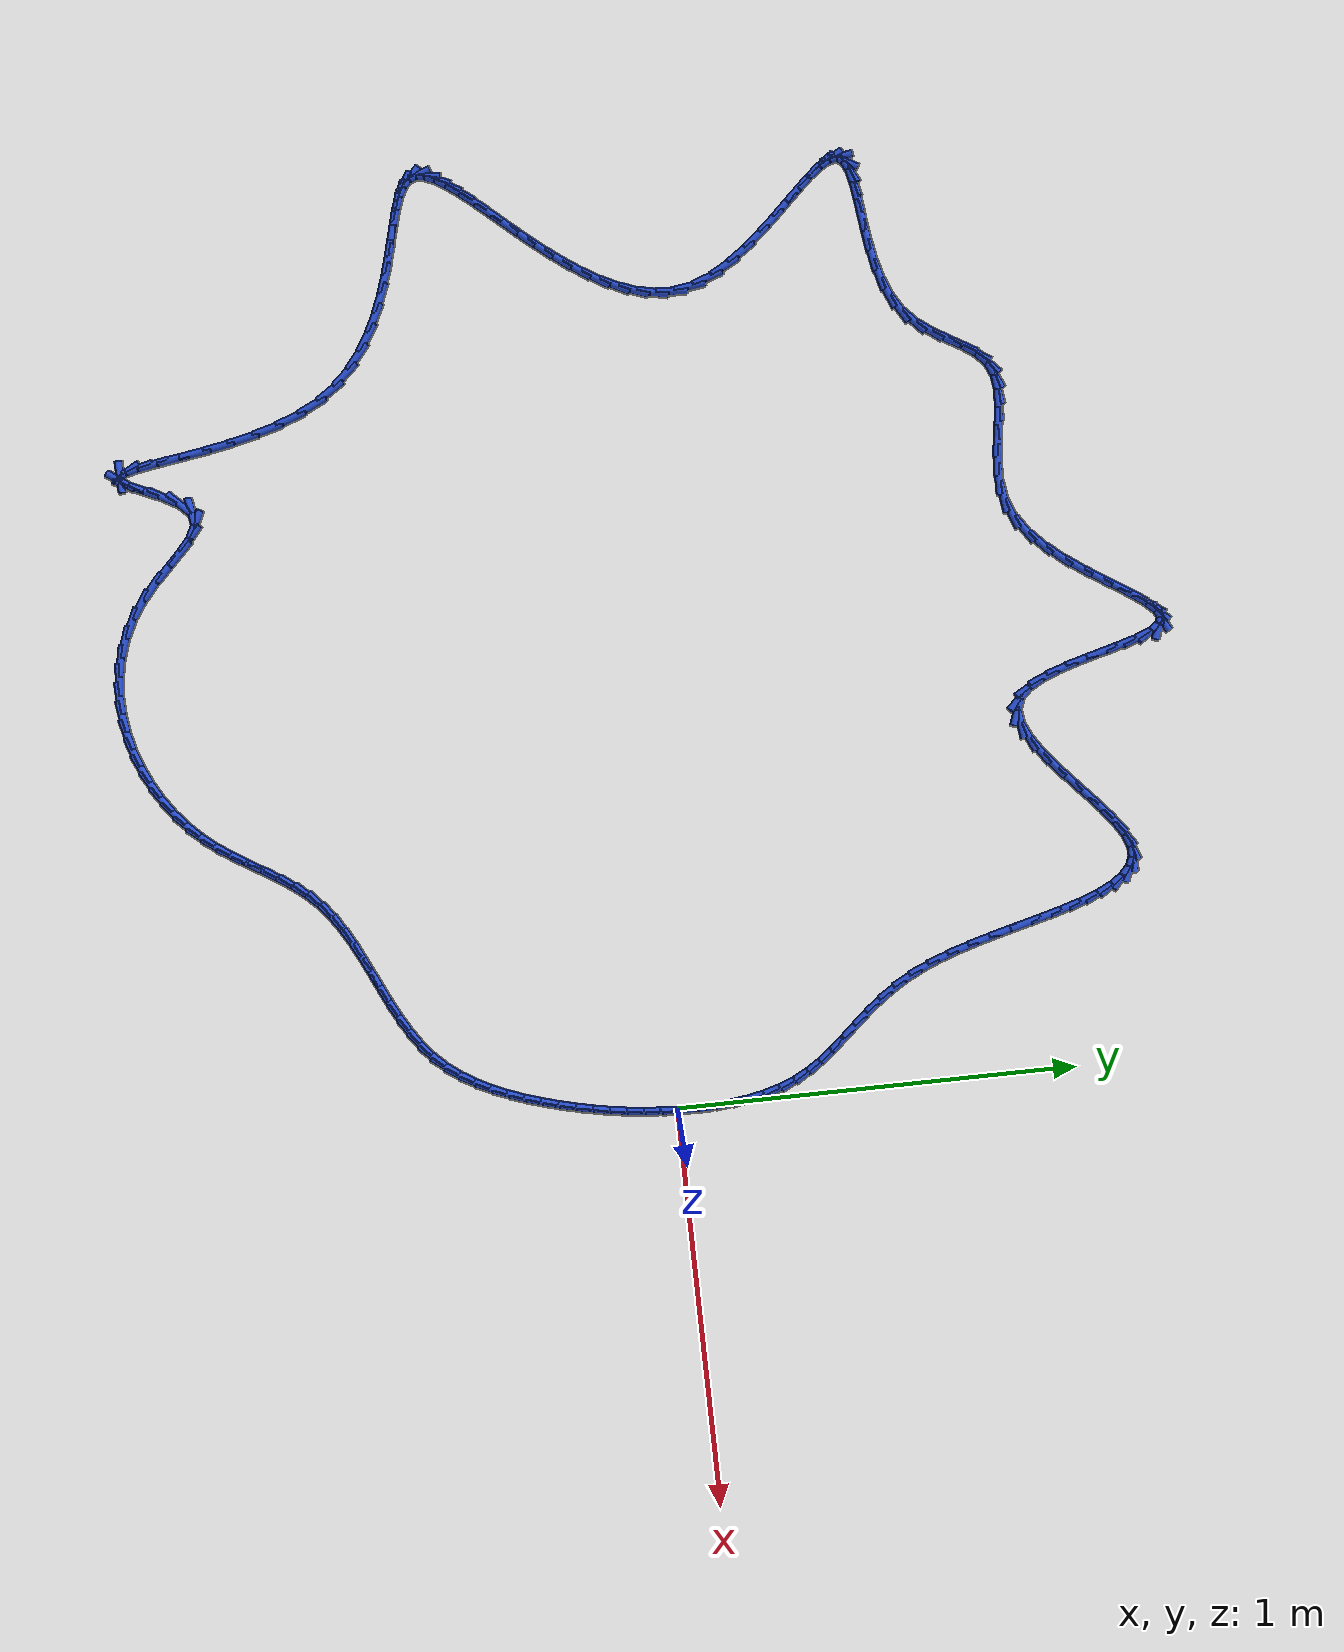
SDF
<sdf version="1.6">
 <world name="default">
  <light name="sun" type="directional">
   <pose>0 0 10 0 -0 0</pose>
   <diffuse>0.8 0.8 0.8 1</diffuse>
   <specular>0.2 0.2 0.2 1</specular>
   <attenuation>
    <range>1000</range>
    <constant>0.9</constant>
    <linear>0.01</linear>
    <quadratic>0.001</quadratic>
   </attenuation>
   <direction>-0.5 0.1 -0.9</direction>
  </light>
  <model name="ground_plane">
   <static>1</static>
   <link name="link">
    <collision name="collision">
     <geometry><plane><normal>0 0 1</normal><size>100 100</size></plane></geometry>
     <surface><friction><ode><mu>100</mu><mu2>50</mu2></ode></friction></surface>
    </collision>
    <visual name="visual">
     <cast_shadows>0</cast_shadows>
     <geometry><plane><normal>0 0 1</normal><size>100 100</size></plane></geometry>
     <material>
      <script><uri>file://media/materials/scripts/gazebo.material</uri><name>Gazebo/WhiteGlow</name></script>
     </material>
    </visual>
   </link>
  </model>
  <gravity>0 0 -9.8</gravity>
  <magnetic_field>6e-06 2.3e-05 -4.2e-05</magnetic_field>
  <atmosphere type="adiabatic"/>
  <physics name="default_physics" default="0" type="ode">
   <max_step_size>0.001</max_step_size>
   <real_time_factor>1</real_time_factor>
   <real_time_update_rate>1000</real_time_update_rate>
  </physics>
  <scene><ambient>0.4 0.4 0.4 1</ambient><background>0.7 0.7 0.7 1</background><shadows>1</shadows></scene>
  <spherical_coordinates>
   <surface_model>EARTH_WGS84</surface_model>
   <latitude_deg>0</latitude_deg>
   <longitude_deg>0</longitude_deg>
   <elevation>0</elevation>
   <heading_deg>0</heading_deg>
  </spherical_coordinates>
  <model name="line">
   <link name="link_0">
    <pose>9.107298248878237e-18 -3.469446951953614e-17 0.01 0 1.57 1.554007148808215</pose>
    <collision name="collision">
     <geometry><cylinder><radius>0.01</radius><length>0.08</length></cylinder></geometry>
    </collision>
    <visual name="visual">
     <material>
      <script><name>Gazebo/Blue</name><uri>file://media/materials/scripts/gazebo.material</uri></script>
     </material>
     <geometry><cylinder><radius>0.01</radius><length>0.08</length></cylinder></geometry>
    </visual>
   </link>
   <link name="link_1">
    <pose>0.0007371283879256532 0.04390084657426722 0.01 0 1.57 -1.5478041733718482</pose>
    <collision name="collision">
     <geometry><cylinder><radius>0.01</radius><length>0.08</length></cylinder></geometry>
    </collision>
    <visual name="visual">
     <material>
      <script><name>Gazebo/Blue</name><uri>file://media/materials/scripts/gazebo.material</uri></script>
     </material>
     <geometry><cylinder><radius>0.01</radius><length>0.08</length></cylinder></geometry>
    </visual>
   </link>
   <link name="link_2">
    <pose>-0.0002791137424871577 0.08809257713083264 0.01 0 1.57 -1.5006837348284627</pose>
    <collision name="collision">
     <geometry><cylinder><radius>0.01</radius><length>0.08</length></cylinder></geometry>
    </collision>
    <visual name="visual">
     <material>
      <script><name>Gazebo/Blue</name><uri>file://media/materials/scripts/gazebo.material</uri></script>
     </material>
     <geometry><cylinder><radius>0.01</radius><length>0.08</length></cylinder></geometry>
    </visual>
   </link>
   <link name="link_3">
    <pose>-0.0033679881207795744 0.13207627860192328 0.01 0 1.57 -1.4448223519250336</pose>
    <collision name="collision">
     <geometry><cylinder><radius>0.01</radius><length>0.08</length></cylinder></geometry>
    </collision>
    <visual name="visual">
     <material>
      <script><name>Gazebo/Blue</name><uri>file://media/materials/scripts/gazebo.material</uri></script>
     </material>
     <geometry><cylinder><radius>0.01</radius><length>0.08</length></cylinder></geometry>
    </visual>
   </link>
   <link name="link_4">
    <pose>-0.008848756476492754 0.17535303791976634 0.01 0 1.57 -1.3784856092452</pose>
    <collision name="collision">
     <geometry><cylinder><radius>0.01</radius><length>0.08</length></cylinder></geometry>
    </collision>
    <visual name="visual">
     <material>
      <script><name>Gazebo/Blue</name><uri>file://media/materials/scripts/gazebo.material</uri></script>
     </material>
     <geometry><cylinder><radius>0.01</radius><length>0.08</length></cylinder></geometry>
    </visual>
   </link>
   <link name="link_5">
    <pose>-0.01704068053916784 0.21742394201658885 0.01 0 1.57 -1.2996304046909632</pose>
    <collision name="collision">
     <geometry><cylinder><radius>0.01</radius><length>0.08</length></cylinder></geometry>
    </collision>
    <visual name="visual">
     <material>
      <script><name>Gazebo/Blue</name><uri>file://media/materials/scripts/gazebo.material</uri></script>
     </material>
     <geometry><cylinder><radius>0.01</radius><length>0.08</length></cylinder></geometry>
    </visual>
   </link>
   <link name="link_6">
    <pose>-0.028263022038345985 0.25779007782461794 0.01 0 1.57 -1.2060408912454148</pose>
    <collision name="collision">
     <geometry><cylinder><radius>0.01</radius><length>0.08</length></cylinder></geometry>
    </collision>
    <visual name="visual">
     <material>
      <script><name>Gazebo/Blue</name><uri>file://media/materials/scripts/gazebo.material</uri></script>
     </material>
     <geometry><cylinder><radius>0.01</radius><length>0.08</length></cylinder></geometry>
    </visual>
   </link>
   <link name="link_7">
    <pose>-0.042835042703568374 0.2959525322760808 0.01 0 1.57 -1.0973697714715052</pose>
    <collision name="collision">
     <geometry><cylinder><radius>0.01</radius><length>0.08</length></cylinder></geometry>
    </collision>
    <visual name="visual">
     <material>
      <script><name>Gazebo/Blue</name><uri>file://media/materials/scripts/gazebo.material</uri></script>
     </material>
     <geometry><cylinder><radius>0.01</radius><length>0.08</length></cylinder></geometry>
    </visual>
   </link>
   <link name="link_8">
    <pose>-0.0610305144496441 0.3314708519281472 0.01 0 1.57 -0.9956041551505752</pose>
    <collision name="collision">
     <geometry><cylinder><radius>0.01</radius><length>0.08</length></cylinder></geometry>
    </collision>
    <visual name="visual">
     <material>
      <script><name>Gazebo/Blue</name><uri>file://media/materials/scripts/gazebo.material</uri></script>
     </material>
     <geometry><cylinder><radius>0.01</radius><length>0.08</length></cylinder></geometry>
    </visual>
   </link>
   <link name="link_9">
    <pose>-0.0825420773117032 0.3646514043995482 0.01 0 1.57 -0.9198542157680601</pose>
    <collision name="collision">
     <geometry><cylinder><radius>0.01</radius><length>0.08</length></cylinder></geometry>
    </collision>
    <visual name="visual">
     <material>
      <script><name>Gazebo/Blue</name><uri>file://media/materials/scripts/gazebo.material</uri></script>
     </material>
     <geometry><cylinder><radius>0.01</radius><length>0.08</length></cylinder></geometry>
    </visual>
   </link>
   <link name="link_10">
    <pose>-0.1066610130613632 0.39631634867222204 0.01 0 1.57 -0.8724217180830622</pose>
    <collision name="collision">
     <geometry><cylinder><radius>0.01</radius><length>0.08</length></cylinder></geometry>
    </collision>
    <visual name="visual">
     <material>
      <script><name>Gazebo/Blue</name><uri>file://media/materials/scripts/gazebo.material</uri></script>
     </material>
     <geometry><cylinder><radius>0.01</radius><length>0.08</length></cylinder></geometry>
    </visual>
   </link>
   <link name="link_11">
    <pose>-0.13267061957796325 0.4272981039446175 0.01 0 1.57 -0.8529867306650798</pose>
    <collision name="collision">
     <geometry><cylinder><radius>0.01</radius><length>0.08</length></cylinder></geometry>
    </collision>
    <visual name="visual">
     <material>
      <script><name>Gazebo/Blue</name><uri>file://media/materials/scripts/gazebo.material</uri></script>
     </material>
     <geometry><cylinder><radius>0.01</radius><length>0.08</length></cylinder></geometry>
    </visual>
   </link>
   <link name="link_12">
    <pose>-0.1598541947408422 0.45842908941518273 0.01 0 1.57 -0.8600962912364204</pose>
    <collision name="collision">
     <geometry><cylinder><radius>0.01</radius><length>0.08</length></cylinder></geometry>
    </collision>
    <visual name="visual">
     <material>
      <script><name>Gazebo/Blue</name><uri>file://media/materials/scripts/gazebo.material</uri></script>
     </material>
     <geometry><cylinder><radius>0.01</radius><length>0.08</length></cylinder></geometry>
    </visual>
   </link>
   <link name="link_13">
    <pose>-0.18749503642933948 0.4905417242823671 0.01 0 1.57 -0.8917560117625842</pose>
    <collision name="collision">
     <geometry><cylinder><radius>0.01</radius><length>0.08</length></cylinder></geometry>
    </collision>
    <visual name="visual">
     <material>
      <script><name>Gazebo/Blue</name><uri>file://media/materials/scripts/gazebo.material</uri></script>
     </material>
     <geometry><cylinder><radius>0.01</radius><length>0.08</length></cylinder></geometry>
    </visual>
   </link>
   <link name="link_14">
    <pose>-0.2148764425227939 0.5244684277446191 0.01 0 1.57 -0.9454676940283231</pose>
    <collision name="collision">
     <geometry><cylinder><radius>0.01</radius><length>0.08</length></cylinder></geometry>
    </collision>
    <visual name="visual">
     <material>
      <script><name>Gazebo/Blue</name><uri>file://media/materials/scripts/gazebo.material</uri></script>
     </material>
     <geometry><cylinder><radius>0.01</radius><length>0.08</length></cylinder></geometry>
    </visual>
   </link>
   <link name="link_15">
    <pose>-0.24128171090054457 0.5610416190003872 0.01 0 1.57 -1.017965380930945</pose>
    <collision name="collision">
     <geometry><cylinder><radius>0.01</radius><length>0.08</length></cylinder></geometry>
    </collision>
    <visual name="visual">
     <material>
      <script><name>Gazebo/Blue</name><uri>file://media/materials/scripts/gazebo.material</uri></script>
     </material>
     <geometry><cylinder><radius>0.01</radius><length>0.08</length></cylinder></geometry>
    </visual>
   </link>
   <link name="link_16">
    <pose>-0.2659941394419307 0.6010937172481206 0.01 0 1.57 -1.1044884392890215</pose>
    <collision name="collision">
     <geometry><cylinder><radius>0.01</radius><length>0.08</length></cylinder></geometry>
    </collision>
    <visual name="visual">
     <material>
      <script><name>Gazebo/Blue</name><uri>file://media/materials/scripts/gazebo.material</uri></script>
     </material>
     <geometry><cylinder><radius>0.01</radius><length>0.08</length></cylinder></geometry>
    </visual>
   </link>
   <link name="link_17">
    <pose>-0.2883113769959543 0.6454329123767709 0.01 0 1.57 -1.1851848594180354</pose>
    <collision name="collision">
     <geometry><cylinder><radius>0.01</radius><length>0.08</length></cylinder></geometry>
    </collision>
    <visual name="visual">
     <material>
      <script><name>Gazebo/Blue</name><uri>file://media/materials/scripts/gazebo.material</uri></script>
     </material>
     <geometry><cylinder><radius>0.01</radius><length>0.08</length></cylinder></geometry>
    </visual>
   </link>
   <link name="link_18">
    <pose>-0.30803390145236614 0.6940184481247369 0.01 0 1.57 -1.2437518622695176</pose>
    <collision name="collision">
     <geometry><cylinder><radius>0.01</radius><length>0.08</length></cylinder></geometry>
    </collision>
    <visual name="visual">
     <material>
      <script><name>Gazebo/Blue</name><uri>file://media/materials/scripts/gazebo.material</uri></script>
     </material>
     <geometry><cylinder><radius>0.01</radius><length>0.08</length></cylinder></geometry>
    </visual>
   </link>
   <link name="link_19">
    <pose>-0.3255852012506695 0.745757714886426 0.01 0 1.57 -1.2840960572406794</pose>
    <collision name="collision">
     <geometry><cylinder><radius>0.01</radius><length>0.08</length></cylinder></geometry>
    </collision>
    <visual name="visual">
     <material>
      <script><name>Gazebo/Blue</name><uri>file://media/materials/scripts/gazebo.material</uri></script>
     </material>
     <geometry><cylinder><radius>0.01</radius><length>0.08</length></cylinder></geometry>
    </visual>
   </link>
   <link name="link_20">
    <pose>-0.34142749870786654 0.7994927071193892 0.01 0 1.57 -1.3094619707613027</pose>
    <collision name="collision">
     <geometry><cylinder><radius>0.01</radius><length>0.08</length></cylinder></geometry>
    </collision>
    <visual name="visual">
     <material>
      <script><name>Gazebo/Blue</name><uri>file://media/materials/scripts/gazebo.material</uri></script>
     </material>
     <geometry><cylinder><radius>0.01</radius><length>0.08</length></cylinder></geometry>
    </visual>
   </link>
   <link name="link_21">
    <pose>-0.35602301614095916 0.8540654192811773 0.01 0 1.57 -1.3215225272024367</pose>
    <collision name="collision">
     <geometry><cylinder><radius>0.01</radius><length>0.08</length></cylinder></geometry>
    </collision>
    <visual name="visual">
     <material>
      <script><name>Gazebo/Blue</name><uri>file://media/materials/scripts/gazebo.material</uri></script>
     </material>
     <geometry><cylinder><radius>0.01</radius><length>0.08</length></cylinder></geometry>
    </visual>
   </link>
   <link name="link_22">
    <pose>-0.3698339758669497 0.9083178458293415 0.01 0 1.57 -1.3205619688914751</pose>
    <collision name="collision">
     <geometry><cylinder><radius>0.01</radius><length>0.08</length></cylinder></geometry>
    </collision>
    <visual name="visual">
     <material>
      <script><name>Gazebo/Blue</name><uri>file://media/materials/scripts/gazebo.material</uri></script>
     </material>
     <geometry><cylinder><radius>0.01</radius><length>0.08</length></cylinder></geometry>
    </visual>
   </link>
   <link name="link_23">
    <pose>-0.3833226002028399 0.9610919812214322 0.01 0 1.57 -1.3053881172568562</pose>
    <collision name="collision">
     <geometry><cylinder><radius>0.01</radius><length>0.08</length></cylinder></geometry>
    </collision>
    <visual name="visual">
     <material>
      <script><name>Gazebo/Blue</name><uri>file://media/materials/scripts/gazebo.material</uri></script>
     </material>
     <geometry><cylinder><radius>0.01</radius><length>0.08</length></cylinder></geometry>
    </visual>
   </link>
   <link name="link_24">
    <pose>-0.3969511114656321 1.0112298199150007 0.01 0 1.57 -1.2728677406237572</pose>
    <collision name="collision">
     <geometry><cylinder><radius>0.01</radius><length>0.08</length></cylinder></geometry>
    </collision>
    <visual name="visual">
     <material>
      <script><name>Gazebo/Blue</name><uri>file://media/materials/scripts/gazebo.material</uri></script>
     </material>
     <geometry><cylinder><radius>0.01</radius><length>0.08</length></cylinder></geometry>
    </visual>
   </link>
   <link name="link_25">
    <pose>-0.4111817319723284 1.057573356367598 0.01 0 1.57 -1.216837287308311</pose>
    <collision name="collision">
     <geometry><cylinder><radius>0.01</radius><length>0.08</length></cylinder></geometry>
    </collision>
    <visual name="visual">
     <material>
      <script><name>Gazebo/Blue</name><uri>file://media/materials/scripts/gazebo.material</uri></script>
     </material>
     <geometry><cylinder><radius>0.01</radius><length>0.08</length></cylinder></geometry>
    </visual>
   </link>
   <link name="link_26">
    <pose>-0.4264766840399307 1.0989645850367746 0.01 0 1.57 -1.1258904108804455</pose>
    <collision name="collision">
     <geometry><cylinder><radius>0.01</radius><length>0.08</length></cylinder></geometry>
    </collision>
    <visual name="visual">
     <material>
      <script><name>Gazebo/Blue</name><uri>file://media/materials/scripts/gazebo.material</uri></script>
     </material>
     <geometry><cylinder><radius>0.01</radius><length>0.08</length></cylinder></geometry>
    </visual>
   </link>
   <link name="link_27">
    <pose>-0.4432981899854412 1.1342455003800818 0.01 0 1.57 -0.9794593696613393</pose>
    <collision name="collision">
     <geometry><cylinder><radius>0.01</radius><length>0.08</length></cylinder></geometry>
    </collision>
    <visual name="visual">
     <material>
      <script><name>Gazebo/Blue</name><uri>file://media/materials/scripts/gazebo.material</uri></script>
     </material>
     <geometry><cylinder><radius>0.01</radius><length>0.08</length></cylinder></geometry>
    </visual>
   </link>
   <link name="link_28">
    <pose>-0.4621084721258619 1.16225809685507 0.01 0 1.57 -0.744414785704542</pose>
    <collision name="collision">
     <geometry><cylinder><radius>0.01</radius><length>0.08</length></cylinder></geometry>
    </collision>
    <visual name="visual">
     <material>
      <script><name>Gazebo/Blue</name><uri>file://media/materials/scripts/gazebo.material</uri></script>
     </material>
     <geometry><cylinder><radius>0.01</radius><length>0.08</length></cylinder></geometry>
    </visual>
   </link>
   <link name="link_29">
    <pose>-0.4833697527781947 1.1818443689192901 0.01 0 1.57 -0.3922942334892025</pose>
    <collision name="collision">
     <geometry><cylinder><radius>0.01</radius><length>0.08</length></cylinder></geometry>
    </collision>
    <visual name="visual">
     <material>
      <script><name>Gazebo/Blue</name><uri>file://media/materials/scripts/gazebo.material</uri></script>
     </material>
     <geometry><cylinder><radius>0.01</radius><length>0.08</length></cylinder></geometry>
    </visual>
   </link>
   <link name="link_30">
    <pose>-0.5075442542594422 1.1918463110302937 0.01 0 1.57 0.026868119838280226</pose>
    <collision name="collision">
     <geometry><cylinder><radius>0.01</radius><length>0.08</length></cylinder></geometry>
    </collision>
    <visual name="visual">
     <material>
      <script><name>Gazebo/Blue</name><uri>file://media/materials/scripts/gazebo.material</uri></script>
     </material>
     <geometry><cylinder><radius>0.01</radius><length>0.08</length></cylinder></geometry>
    </visual>
   </link>
   <link name="link_31">
    <pose>-0.535094198886606 1.191105917645631 0.01 0 1.57 0.3746171646383171</pose>
    <collision name="collision">
     <geometry><cylinder><radius>0.01</radius><length>0.08</length></cylinder></geometry>
    </collision>
    <visual name="visual">
     <material>
      <script><name>Gazebo/Blue</name><uri>file://media/materials/scripts/gazebo.material</uri></script>
     </material>
     <geometry><cylinder><radius>0.01</radius><length>0.08</length></cylinder></geometry>
    </visual>
   </link>
   <link name="link_32">
    <pose>-0.5663703722770722 1.1788086113641076 0.01 0 1.57 0.5713890799570683</pose>
    <collision name="collision">
     <geometry><cylinder><radius>0.01</radius><length>0.08</length></cylinder></geometry>
    </collision>
    <visual name="visual">
     <material>
      <script><name>Gazebo/Blue</name><uri>file://media/materials/scripts/gazebo.material</uri></script>
     </material>
     <geometry><cylinder><radius>0.01</radius><length>0.08</length></cylinder></geometry>
    </visual>
   </link>
   <link name="link_33">
    <pose>-0.6009284577402193 1.1565901790602746 0.01 0 1.57 0.6714211400236234</pose>
    <collision name="collision">
     <geometry><cylinder><radius>0.01</radius><length>0.08</length></cylinder></geometry>
    </collision>
    <visual name="visual">
     <material>
      <script><name>Gazebo/Blue</name><uri>file://media/materials/scripts/gazebo.material</uri></script>
     </material>
     <geometry><cylinder><radius>0.01</radius><length>0.08</length></cylinder></geometry>
    </visual>
   </link>
   <link name="link_34">
    <pose>-0.6379786200959717 1.1271512343041146 0.01 0 1.57 0.7195220363019236</pose>
    <collision name="collision">
     <geometry><cylinder><radius>0.01</radius><length>0.08</length></cylinder></geometry>
    </collision>
    <visual name="visual">
     <material>
      <script><name>Gazebo/Blue</name><uri>file://media/materials/scripts/gazebo.material</uri></script>
     </material>
     <geometry><cylinder><radius>0.01</radius><length>0.08</length></cylinder></geometry>
    </visual>
   </link>
   <link name="link_35">
    <pose>-0.6767296137997205 1.0931967371589302 0.01 0 1.57 0.7337972690347124</pose>
    <collision name="collision">
     <geometry><cylinder><radius>0.01</radius><length>0.08</length></cylinder></geometry>
    </collision>
    <visual name="visual">
     <material>
      <script><name>Gazebo/Blue</name><uri>file://media/materials/scripts/gazebo.material</uri></script>
     </material>
     <geometry><cylinder><radius>0.01</radius><length>0.08</length></cylinder></geometry>
    </visual>
   </link>
   <link name="link_36">
    <pose>-0.7163901933068564 1.0574316476880232 0.01 0 1.57 0.719742877539613</pose>
    <collision name="collision">
     <geometry><cylinder><radius>0.01</radius><length>0.08</length></cylinder></geometry>
    </collision>
    <visual name="visual">
     <material>
      <script><name>Gazebo/Blue</name><uri>file://media/materials/scripts/gazebo.material</uri></script>
     </material>
     <geometry><cylinder><radius>0.01</radius><length>0.08</length></cylinder></geometry>
    </visual>
   </link>
   <link name="link_37">
    <pose>-0.7561691130727703 1.0225609259546955 0.01 0 1.57 0.6745316939928019</pose>
    <collision name="collision">
     <geometry><cylinder><radius>0.01</radius><length>0.08</length></cylinder></geometry>
    </collision>
    <visual name="visual">
     <material>
      <script><name>Gazebo/Blue</name><uri>file://media/materials/scripts/gazebo.material</uri></script>
     </material>
     <geometry><cylinder><radius>0.01</radius><length>0.08</length></cylinder></geometry>
    </visual>
   </link>
   <link name="link_38">
    <pose>-0.7952751275528531 0.9912895320222496 0.01 0 1.57 0.5856545201994937</pose>
    <collision name="collision">
     <geometry><cylinder><radius>0.01</radius><length>0.08</length></cylinder></geometry>
    </collision>
    <visual name="visual">
     <material>
      <script><name>Gazebo/Blue</name><uri>file://media/materials/scripts/gazebo.material</uri></script>
     </material>
     <geometry><cylinder><radius>0.01</radius><length>0.08</length></cylinder></geometry>
    </visual>
   </link>
   <link name="link_39">
    <pose>-0.8329169912024958 0.9663224259539875 0.01 0 1.57 0.42365143261723803</pose>
    <collision name="collision">
     <geometry><cylinder><radius>0.01</radius><length>0.08</length></cylinder></geometry>
    </collision>
    <visual name="visual">
     <material>
      <script><name>Gazebo/Blue</name><uri>file://media/materials/scripts/gazebo.material</uri></script>
     </material>
     <geometry><cylinder><radius>0.01</radius><length>0.08</length></cylinder></geometry>
    </visual>
   </link>
   <link name="link_40">
    <pose>-0.8683034584770891 0.9503645678132113 0.01 0 1.57 0.1304750963226663</pose>
    <collision name="collision">
     <geometry><cylinder><radius>0.01</radius><length>0.08</length></cylinder></geometry>
    </collision>
    <visual name="visual">
     <material>
      <script><name>Gazebo/Blue</name><uri>file://media/materials/scripts/gazebo.material</uri></script>
     </material>
     <geometry><cylinder><radius>0.01</radius><length>0.08</length></cylinder></geometry>
    </visual>
   </link>
   <link name="link_41">
    <pose>-0.9006432838320237 0.9461209176632231 0.01 0 1.57 -0.3424716379809914</pose>
    <collision name="collision">
     <geometry><cylinder><radius>0.01</radius><length>0.08</length></cylinder></geometry>
    </collision>
    <visual name="visual">
     <material>
      <script><name>Gazebo/Blue</name><uri>file://media/materials/scripts/gazebo.material</uri></script>
     </material>
     <geometry><cylinder><radius>0.01</radius><length>0.08</length></cylinder></geometry>
    </visual>
   </link>
   <link name="link_42">
    <pose>-0.9291482684194343 0.9562835213448168 0.01 0 1.57 -0.8061007375267966</pose>
    <collision name="collision">
     <geometry><cylinder><radius>0.01</radius><length>0.08</length></cylinder></geometry>
    </collision>
    <visual name="visual">
     <material>
      <script><name>Gazebo/Blue</name><uri>file://media/materials/scripts/gazebo.material</uri></script>
     </material>
     <geometry><cylinder><radius>0.01</radius><length>0.08</length></cylinder></geometry>
    </visual>
   </link>
   <link name="link_43">
    <pose>-0.9534788120531184 0.9816429217201903 0.01 0 1.57 -1.0652152955537457</pose>
    <collision name="collision">
     <geometry><cylinder><radius>0.01</radius><length>0.08</length></cylinder></geometry>
    </collision>
    <visual name="visual">
     <material>
      <script><name>Gazebo/Blue</name><uri>file://media/materials/scripts/gazebo.material</uri></script>
     </material>
     <geometry><cylinder><radius>0.01</radius><length>0.08</length></cylinder></geometry>
    </visual>
   </link>
   <link name="link_44">
    <pose>-0.974213261416617 1.0190987033046222 0.01 0 1.57 -1.2008590520488491</pose>
    <collision name="collision">
     <geometry><cylinder><radius>0.01</radius><length>0.08</length></cylinder></geometry>
    </collision>
    <visual name="visual">
     <material>
      <script><name>Gazebo/Blue</name><uri>file://media/materials/scripts/gazebo.material</uri></script>
     </material>
     <geometry><cylinder><radius>0.01</radius><length>0.08</length></cylinder></geometry>
    </visual>
   </link>
   <link name="link_45">
    <pose>-0.9920422534735659 1.0650744788365782 0.01 0 1.57 -1.2732544466909295</pose>
    <collision name="collision">
     <geometry><cylinder><radius>0.01</radius><length>0.08</length></cylinder></geometry>
    </collision>
    <visual name="visual">
     <material>
      <script><name>Gazebo/Blue</name><uri>file://media/materials/scripts/gazebo.material</uri></script>
     </material>
     <geometry><cylinder><radius>0.01</radius><length>0.08</length></cylinder></geometry>
    </visual>
   </link>
   <link name="link_46">
    <pose>-1.0076564251876006 1.1159938610545233 0.01 0 1.57 -1.3075728800612978</pose>
    <collision name="collision">
     <geometry><cylinder><radius>0.01</radius><length>0.08</length></cylinder></geometry>
    </collision>
    <visual name="visual">
     <material>
      <script><name>Gazebo/Blue</name><uri>file://media/materials/scripts/gazebo.material</uri></script>
     </material>
     <geometry><cylinder><radius>0.01</radius><length>0.08</length></cylinder></geometry>
    </visual>
   </link>
   <link name="link_47">
    <pose>-1.0217464135223568 1.1682804626969236 0.01 0 1.57 -1.3120132933813489</pose>
    <collision name="collision">
     <geometry><cylinder><radius>0.01</radius><length>0.08</length></cylinder></geometry>
    </collision>
    <visual name="visual">
     <material>
      <script><name>Gazebo/Blue</name><uri>file://media/materials/scripts/gazebo.material</uri></script>
     </material>
     <geometry><cylinder><radius>0.01</radius><length>0.08</length></cylinder></geometry>
    </visual>
   </link>
   <link name="link_48">
    <pose>-1.03500285544147 1.2183578965022444 0.01 0 1.57 -1.2829481793455673</pose>
    <collision name="collision">
     <geometry><cylinder><radius>0.01</radius><length>0.08</length></cylinder></geometry>
    </collision>
    <visual name="visual">
     <material>
      <script><name>Gazebo/Blue</name><uri>file://media/materials/scripts/gazebo.material</uri></script>
     </material>
     <geometry><cylinder><radius>0.01</radius><length>0.08</length></cylinder></geometry>
    </visual>
   </link>
   <link name="link_49">
    <pose>-1.0481163879085766 1.2626497752089523 0.01 0 1.57 -1.1979818109754052</pose>
    <collision name="collision">
     <geometry><cylinder><radius>0.01</radius><length>0.08</length></cylinder></geometry>
    </collision>
    <visual name="visual">
     <material>
      <script><name>Gazebo/Blue</name><uri>file://media/materials/scripts/gazebo.material</uri></script>
     </material>
     <geometry><cylinder><radius>0.01</radius><length>0.08</length></cylinder></geometry>
    </visual>
   </link>
   <link name="link_50">
    <pose>-1.0617776478873115 1.2975797115555114 0.01 0 1.57 -0.9753214857243382</pose>
    <collision name="collision">
     <geometry><cylinder><radius>0.01</radius><length>0.08</length></cylinder></geometry>
    </collision>
    <visual name="visual">
     <material>
      <script><name>Gazebo/Blue</name><uri>file://media/materials/scripts/gazebo.material</uri></script>
     </material>
     <geometry><cylinder><radius>0.01</radius><length>0.08</length></cylinder></geometry>
    </visual>
   </link>
   <link name="link_51">
    <pose>-1.076677272341311 1.319571318280389 0.01 0 1.57 -0.3417042652146167</pose>
    <collision name="collision">
     <geometry><cylinder><radius>0.01</radius><length>0.08</length></cylinder></geometry>
    </collision>
    <visual name="visual">
     <material>
      <script><name>Gazebo/Blue</name><uri>file://media/materials/scripts/gazebo.material</uri></script>
     </material>
     <geometry><cylinder><radius>0.01</radius><length>0.08</length></cylinder></geometry>
    </visual>
   </link>
   <link name="link_52">
    <pose>-1.0934564583698798 1.3255389290189208 0.01 0 1.57 0.4554692151168353</pose>
    <collision name="collision">
     <geometry><cylinder><radius>0.01</radius><length>0.08</length></cylinder></geometry>
    </collision>
    <visual name="visual">
     <material>
      <script><name>Gazebo/Blue</name><uri>file://media/materials/scripts/gazebo.material</uri></script>
     </material>
     <geometry><cylinder><radius>0.01</radius><length>0.08</length></cylinder></geometry>
    </visual>
   </link>
   <link name="link_53">
    <pose>-1.1123654891166563 1.316276937546561 0.01 0 1.57 0.8028645329625573</pose>
    <collision name="collision">
     <geometry><cylinder><radius>0.01</radius><length>0.08</length></cylinder></geometry>
    </collision>
    <visual name="visual">
     <material>
      <script><name>Gazebo/Blue</name><uri>file://media/materials/scripts/gazebo.material</uri></script>
     </material>
     <geometry><cylinder><radius>0.01</radius><length>0.08</length></cylinder></geometry>
    </visual>
   </link>
   <link name="link_54">
    <pose>-1.133468928514187 1.2944231144171385 0.01 0 1.57 0.9371542961048148</pose>
    <collision name="collision">
     <geometry><cylinder><radius>0.01</radius><length>0.08</length></cylinder></geometry>
    </collision>
    <visual name="visual">
     <material>
      <script><name>Gazebo/Blue</name><uri>file://media/materials/scripts/gazebo.material</uri></script>
     </material>
     <geometry><cylinder><radius>0.01</radius><length>0.08</length></cylinder></geometry>
    </visual>
   </link>
   <link name="link_55">
    <pose>-1.1568302141045534 1.262626410298869 0.01 0 1.57 0.9895155194570046</pose>
    <collision name="collision">
     <geometry><cylinder><radius>0.01</radius><length>0.08</length></cylinder></geometry>
    </collision>
    <visual name="visual">
     <material>
      <script><name>Gazebo/Blue</name><uri>file://media/materials/scripts/gazebo.material</uri></script>
     </material>
     <geometry><cylinder><radius>0.01</radius><length>0.08</length></cylinder></geometry>
    </visual>
   </link>
   <link name="link_56">
    <pose>-1.1825127834298388 1.2235357758599676 0.01 0 1.57 1.0002432786251882</pose>
    <collision name="collision">
     <geometry><cylinder><radius>0.01</radius><length>0.08</length></cylinder></geometry>
    </collision>
    <visual name="visual">
     <material>
      <script><name>Gazebo/Blue</name><uri>file://media/materials/scripts/gazebo.material</uri></script>
     </material>
     <geometry><cylinder><radius>0.01</radius><length>0.08</length></cylinder></geometry>
    </visual>
   </link>
   <link name="link_57">
    <pose>-1.2105800740321246 1.17980016176865 0.01 0 1.57 0.9823746955705589</pose>
    <collision name="collision">
     <geometry><cylinder><radius>0.01</radius><length>0.08</length></cylinder></geometry>
    </collision>
    <visual name="visual">
     <material>
      <script><name>Gazebo/Blue</name><uri>file://media/materials/scripts/gazebo.material</uri></script>
     </material>
     <geometry><cylinder><radius>0.01</radius><length>0.08</length></cylinder></geometry>
    </visual>
   </link>
   <link name="link_58">
    <pose>-1.2410955234534937 1.134068518693133 0.01 0 1.57 0.9384902605620125</pose>
    <collision name="collision">
     <geometry><cylinder><radius>0.01</radius><length>0.08</length></cylinder></geometry>
    </collision>
    <visual name="visual">
     <material>
      <script><name>Gazebo/Blue</name><uri>file://media/materials/scripts/gazebo.material</uri></script>
     </material>
     <geometry><cylinder><radius>0.01</radius><length>0.08</length></cylinder></geometry>
    </visual>
   </link>
   <link name="link_59">
    <pose>-1.274122569236028 1.0889897973016298 0.01 0 1.57 0.865028529700913</pose>
    <collision name="collision">
     <geometry><cylinder><radius>0.01</radius><length>0.08</length></cylinder></geometry>
    </collision>
    <visual name="visual">
     <material>
      <script><name>Gazebo/Blue</name><uri>file://media/materials/scripts/gazebo.material</uri></script>
     </material>
     <geometry><cylinder><radius>0.01</radius><length>0.08</length></cylinder></geometry>
    </visual>
   </link>
   <link name="link_60">
    <pose>-1.3097246489218104 1.0472129482623578 0.01 0 1.57 0.7528103156980193</pose>
    <collision name="collision">
     <geometry><cylinder><radius>0.01</radius><length>0.08</length></cylinder></geometry>
    </collision>
    <visual name="visual">
     <material>
      <script><name>Gazebo/Blue</name><uri>file://media/materials/scripts/gazebo.material</uri></script>
     </material>
     <geometry><cylinder><radius>0.01</radius><length>0.08</length></cylinder></geometry>
    </visual>
   </link>
   <link name="link_61">
    <pose>-1.3479652000529228 1.0113869222435319 0.01 0 1.57 0.5868396788671997</pose>
    <collision name="collision">
     <geometry><cylinder><radius>0.01</radius><length>0.08</length></cylinder></geometry>
    </collision>
    <visual name="visual">
     <material>
      <script><name>Gazebo/Blue</name><uri>file://media/materials/scripts/gazebo.material</uri></script>
     </material>
     <geometry><cylinder><radius>0.01</radius><length>0.08</length></cylinder></geometry>
    </visual>
   </link>
   <link name="link_62">
    <pose>-1.3889076601714474 0.9841606699133674 0.01 0 1.57 0.3581391807869256</pose>
    <collision name="collision">
     <geometry><cylinder><radius>0.01</radius><length>0.08</length></cylinder></geometry>
    </collision>
    <visual name="visual">
     <material>
      <script><name>Gazebo/Blue</name><uri>file://media/materials/scripts/gazebo.material</uri></script>
     </material>
     <geometry><cylinder><radius>0.01</radius><length>0.08</length></cylinder></geometry>
    </visual>
   </link>
   <link name="link_63">
    <pose>-1.4325448660186675 0.9678281418438192 0.01 0 1.57 0.13950697402411846</pose>
    <collision name="collision">
     <geometry><cylinder><radius>0.01</radius><length>0.08</length></cylinder></geometry>
    </collision>
    <visual name="visual">
     <material>
      <script><name>Gazebo/Blue</name><uri>file://media/materials/scripts/gazebo.material</uri></script>
     </material>
     <geometry><cylinder><radius>0.01</radius><length>0.08</length></cylinder></geometry>
    </visual>
   </link>
   <link name="link_64">
    <pose>-1.4782195803113705 0.9614145389799112 0.01 0 1.57 -0.016452622815223698</pose>
    <collision name="collision">
     <geometry><cylinder><radius>0.01</radius><length>0.08</length></cylinder></geometry>
    </collision>
    <visual name="visual">
     <material>
      <script><name>Gazebo/Blue</name><uri>file://media/materials/scripts/gazebo.material</uri></script>
     </material>
     <geometry><cylinder><radius>0.01</radius><length>0.08</length></cylinder></geometry>
    </visual>
   </link>
   <link name="link_65">
    <pose>-1.5249241389938384 0.9621830208087241 0.01 0 1.57 -0.11076613675632105</pose>
    <collision name="collision">
     <geometry><cylinder><radius>0.01</radius><length>0.08</length></cylinder></geometry>
    </collision>
    <visual name="visual">
     <material>
      <script><name>Gazebo/Blue</name><uri>file://media/materials/scripts/gazebo.material</uri></script>
     </material>
     <geometry><cylinder><radius>0.01</radius><length>0.08</length></cylinder></geometry>
    </visual>
   </link>
   <link name="link_66">
    <pose>-1.571647478827977 0.9673796548005772 0.01 0 1.57 -0.14912935221293497</pose>
    <collision name="collision">
     <geometry><cylinder><radius>0.01</radius><length>0.08</length></cylinder></geometry>
    </collision>
    <visual name="visual">
     <material>
      <script><name>Gazebo/Blue</name><uri>file://media/materials/scripts/gazebo.material</uri></script>
     </material>
     <geometry><cylinder><radius>0.01</radius><length>0.08</length></cylinder></geometry>
    </visual>
   </link>
   <link name="link_67">
    <pose>-1.6173785365756927 0.9742505084257914 0.01 0 1.57 -0.13167016068354884</pose>
    <collision name="collision">
     <geometry><cylinder><radius>0.01</radius><length>0.08</length></cylinder></geometry>
    </collision>
    <visual name="visual">
     <material>
      <script><name>Gazebo/Blue</name><uri>file://media/materials/scripts/gazebo.material</uri></script>
     </material>
     <geometry><cylinder><radius>0.01</radius><length>0.08</length></cylinder></geometry>
    </visual>
   </link>
   <link name="link_68">
    <pose>-1.6611062489988917 0.980041649154686 0.01 0 1.57 -0.04804299417828327</pose>
    <collision name="collision">
     <geometry><cylinder><radius>0.01</radius><length>0.08</length></cylinder></geometry>
    </collision>
    <visual name="visual">
     <material>
      <script><name>Gazebo/Blue</name><uri>file://media/materials/scripts/gazebo.material</uri></script>
     </material>
     <geometry><cylinder><radius>0.01</radius><length>0.08</length></cylinder></geometry>
    </visual>
   </link>
   <link name="link_69">
    <pose>-1.7018195528594793 0.9819991444575814 0.01 0 1.57 0.12553845731804164</pose>
    <collision name="collision">
     <geometry><cylinder><radius>0.01</radius><length>0.08</length></cylinder></geometry>
    </collision>
    <visual name="visual">
     <material>
      <script><name>Gazebo/Blue</name><uri>file://media/materials/scripts/gazebo.material</uri></script>
     </material>
     <geometry><cylinder><radius>0.01</radius><length>0.08</length></cylinder></geometry>
    </visual>
   </link>
   <link name="link_70">
    <pose>-1.7385073849193629 0.9773690618047979 0.01 0 1.57 0.41567508856843777</pose>
    <collision name="collision">
     <geometry><cylinder><radius>0.01</radius><length>0.08</length></cylinder></geometry>
    </collision>
    <visual name="visual">
     <material>
      <script><name>Gazebo/Blue</name><uri>file://media/materials/scripts/gazebo.material</uri></script>
     </material>
     <geometry><cylinder><radius>0.01</radius><length>0.08</length></cylinder></geometry>
    </visual>
   </link>
   <link name="link_71">
    <pose>-1.7701590706205068 0.9633981628945976 0.01 0 1.57 0.7542030344829451</pose>
    <collision name="collision">
     <geometry><cylinder><radius>0.01</radius><length>0.08</length></cylinder></geometry>
    </collision>
    <visual name="visual">
     <material>
      <script><name>Gazebo/Blue</name><uri>file://media/materials/scripts/gazebo.material</uri></script>
     </material>
     <geometry><cylinder><radius>0.01</radius><length>0.08</length></cylinder></geometry>
    </visual>
   </link>
   <link name="link_72">
    <pose>-1.7965012951265034 0.9386502199335118 0.01 0 1.57 0.9601447073777327</pose>
    <collision name="collision">
     <geometry><cylinder><radius>0.01</radius><length>0.08</length></cylinder></geometry>
    </collision>
    <visual name="visual">
     <material>
      <script><name>Gazebo/Blue</name><uri>file://media/materials/scripts/gazebo.material</uri></script>
     </material>
     <geometry><cylinder><radius>0.01</radius><length>0.08</length></cylinder></geometry>
    </visual>
   </link>
   <link name="link_73">
    <pose>-1.819531462437243 0.9057447739489267 0.01 0 1.57 1.039166689668857</pose>
    <collision name="collision">
     <geometry><cylinder><radius>0.01</radius><length>0.08</length></cylinder></geometry>
    </collision>
    <visual name="visual">
     <material>
      <script><name>Gazebo/Blue</name><uri>file://media/materials/scripts/gazebo.material</uri></script>
     </material>
     <geometry><cylinder><radius>0.01</radius><length>0.08</length></cylinder></geometry>
    </visual>
   </link>
   <link name="link_74">
    <pose>-1.8416826750490403 0.8680795743262375 0.01 0 1.57 1.0249489774149831</pose>
    <collision name="collision">
     <geometry><cylinder><radius>0.01</radius><length>0.08</length></cylinder></geometry>
    </collision>
    <visual name="visual">
     <material>
      <script><name>Gazebo/Blue</name><uri>file://media/materials/scripts/gazebo.material</uri></script>
     </material>
     <geometry><cylinder><radius>0.01</radius><length>0.08</length></cylinder></geometry>
    </visual>
   </link>
   <link name="link_75">
    <pose>-1.8653880354582113 0.829052370450841 0.01 0 1.57 0.9281778795621108</pose>
    <collision name="collision">
     <geometry><cylinder><radius>0.01</radius><length>0.08</length></cylinder></geometry>
    </collision>
    <visual name="visual">
     <material>
      <script><name>Gazebo/Blue</name><uri>file://media/materials/scripts/gazebo.material</uri></script>
     </material>
     <geometry><cylinder><radius>0.01</radius><length>0.08</length></cylinder></geometry>
    </visual>
   </link>
   <link name="link_76">
    <pose>-1.8930806461610705 0.7920609117081325 0.01 0 1.57 0.7467565721539928</pose>
    <collision name="collision">
     <geometry><cylinder><radius>0.01</radius><length>0.08</length></cylinder></geometry>
    </collision>
    <visual name="visual">
     <material>
      <script><name>Gazebo/Blue</name><uri>file://media/materials/scripts/gazebo.material</uri></script>
     </material>
     <geometry><cylinder><radius>0.01</radius><length>0.08</length></cylinder></geometry>
    </visual>
   </link>
   <link name="link_77">
    <pose>-1.9271855895677508 0.7604948637035878 0.01 0 1.57 0.526431533811003</pose>
    <collision name="collision">
     <geometry><cylinder><radius>0.01</radius><length>0.08</length></cylinder></geometry>
    </collision>
    <visual name="visual">
     <material>
      <script><name>Gazebo/Blue</name><uri>file://media/materials/scripts/gazebo.material</uri></script>
     </material>
     <geometry><cylinder><radius>0.01</radius><length>0.08</length></cylinder></geometry>
    </visual>
   </link>
   <link name="link_78">
    <pose>-1.9687408076876687 0.7363457352820963 0.01 0 1.57 0.359871620331911</pose>
    <collision name="collision">
     <geometry><cylinder><radius>0.01</radius><length>0.08</length></cylinder></geometry>
    </collision>
    <visual name="visual">
     <material>
      <script><name>Gazebo/Blue</name><uri>file://media/materials/scripts/gazebo.material</uri></script>
     </material>
     <geometry><cylinder><radius>0.01</radius><length>0.08</length></cylinder></geometry>
    </visual>
   </link>
   <link name="link_79">
    <pose>-2.0158305776954957 0.7186279131060516 0.01 0 1.57 0.2463112940243135</pose>
    <collision name="collision">
     <geometry><cylinder><radius>0.01</radius><length>0.08</length></cylinder></geometry>
    </collision>
    <visual name="visual">
     <material>
      <script><name>Gazebo/Blue</name><uri>file://media/materials/scripts/gazebo.material</uri></script>
     </material>
     <geometry><cylinder><radius>0.01</radius><length>0.08</length></cylinder></geometry>
    </visual>
   </link>
   <link name="link_80">
    <pose>-2.066160536425164 0.705974136419919 0.01 0 1.57 0.17293776912853898</pose>
    <collision name="collision">
     <geometry><cylinder><radius>0.01</radius><length>0.08</length></cylinder></geometry>
    </collision>
    <visual name="visual">
     <material>
      <script><name>Gazebo/Blue</name><uri>file://media/materials/scripts/gazebo.material</uri></script>
     </material>
     <geometry><cylinder><radius>0.01</radius><length>0.08</length></cylinder></geometry>
    </visual>
   </link>
   <link name="link_81">
    <pose>-2.117436320710603 0.6970171444681639 0.01 0 1.57 0.13197098281103026</pose>
    <collision name="collision">
     <geometry><cylinder><radius>0.01</radius><length>0.08</length></cylinder></geometry>
    </collision>
    <visual name="visual">
     <material>
      <script><name>Gazebo/Blue</name><uri>file://media/materials/scripts/gazebo.material</uri></script>
     </material>
     <geometry><cylinder><radius>0.01</radius><length>0.08</length></cylinder></geometry>
    </visual>
   </link>
   <link name="link_82">
    <pose>-2.1673635673857468 0.690389676495252 0.01 0 1.57 0.12179419795839708</pose>
    <collision name="collision">
     <geometry><cylinder><radius>0.01</radius><length>0.08</length></cylinder></geometry>
    </collision>
    <visual name="visual">
     <material>
      <script><name>Gazebo/Blue</name><uri>file://media/materials/scripts/gazebo.material</uri></script>
     </material>
     <geometry><cylinder><radius>0.01</radius><length>0.08</length></cylinder></geometry>
    </visual>
   </link>
   <link name="link_83">
    <pose>-2.213647913284525 0.6847244717456485 0.01 0 1.57 0.1493296237370794</pose>
    <collision name="collision">
     <geometry><cylinder><radius>0.01</radius><length>0.08</length></cylinder></geometry>
    </collision>
    <visual name="visual">
     <material>
      <script><name>Gazebo/Blue</name><uri>file://media/materials/scripts/gazebo.material</uri></script>
     </material>
     <geometry><cylinder><radius>0.01</radius><length>0.08</length></cylinder></geometry>
    </visual>
   </link>
   <link name="link_84">
    <pose>-2.2539949952408684 0.6786542694638193 0.01 0 1.57 0.23950851110521143</pose>
    <collision name="collision">
     <geometry><cylinder><radius>0.01</radius><length>0.08</length></cylinder></geometry>
    </collision>
    <visual name="visual">
     <material>
      <script><name>Gazebo/Blue</name><uri>file://media/materials/scripts/gazebo.material</uri></script>
     </material>
     <geometry><cylinder><radius>0.01</radius><length>0.08</length></cylinder></geometry>
    </visual>
   </link>
   <link name="link_85">
    <pose>-2.28611045008871 0.6708118088942296 0.01 0 1.57 0.47056198124898824</pose>
    <collision name="collision">
     <geometry><cylinder><radius>0.01</radius><length>0.08</length></cylinder></geometry>
    </collision>
    <visual name="visual">
     <material>
      <script><name>Gazebo/Blue</name><uri>file://media/materials/scripts/gazebo.material</uri></script>
     </material>
     <geometry><cylinder><radius>0.01</radius><length>0.08</length></cylinder></geometry>
    </visual>
   </link>
   <link name="link_86">
    <pose>-2.307699914661982 0.6598298292813456 0.01 0 1.57 1.0471923221539925</pose>
    <collision name="collision">
     <geometry><cylinder><radius>0.01</radius><length>0.08</length></cylinder></geometry>
    </collision>
    <visual name="visual">
     <material>
      <script><name>Gazebo/Blue</name><uri>file://media/materials/scripts/gazebo.material</uri></script>
     </material>
     <geometry><cylinder><radius>0.01</radius><length>0.08</length></cylinder></geometry>
    </visual>
   </link>
   <link name="link_87">
    <pose>-2.3166093444651037 0.644398430545335 0.01 0 1.57 -1.3933457706968422</pose>
    <collision name="collision">
     <geometry><cylinder><radius>0.01</radius><length>0.08</length></cylinder></geometry>
    </collision>
    <visual name="visual">
     <material>
      <script><name>Gazebo/Blue</name><uri>file://media/materials/scripts/gazebo.material</uri></script>
     </material>
     <geometry><cylinder><radius>0.01</radius><length>0.08</length></cylinder></geometry>
    </visual>
   </link>
   <link name="link_88">
    <pose>-2.3129771274279105 0.6241448328945437 0.01 0 1.57 -1.0497855653488857</pose>
    <collision name="collision">
     <geometry><cylinder><radius>0.01</radius><length>0.08</length></cylinder></geometry>
    </collision>
    <visual name="visual">
     <material>
      <script><name>Gazebo/Blue</name><uri>file://media/materials/scripts/gazebo.material</uri></script>
     </material>
     <geometry><cylinder><radius>0.01</radius><length>0.08</length></cylinder></geometry>
    </visual>
   </link>
   <link name="link_89">
    <pose>-2.2988105153960134 0.5994602268388609 0.01 0 1.57 -0.9029433997256386</pose>
    <collision name="collision">
     <geometry><cylinder><radius>0.01</radius><length>0.08</length></cylinder></geometry>
    </collision>
    <visual name="visual">
     <material>
      <script><name>Gazebo/Blue</name><uri>file://media/materials/scripts/gazebo.material</uri></script>
     </material>
     <geometry><cylinder><radius>0.01</radius><length>0.08</length></cylinder></geometry>
    </visual>
   </link>
   <link name="link_90">
    <pose>-2.2761712554295452 0.5707580799117309 0.01 0 1.57 -0.8384164140941982</pose>
    <collision name="collision">
     <geometry><cylinder><radius>0.01</radius><length>0.08</length></cylinder></geometry>
    </collision>
    <visual name="visual">
     <material>
      <script><name>Gazebo/Blue</name><uri>file://media/materials/scripts/gazebo.material</uri></script>
     </material>
     <geometry><cylinder><radius>0.01</radius><length>0.08</length></cylinder></geometry>
    </visual>
   </link>
   <link name="link_91">
    <pose>-2.247121094588639 0.5384518596465974 0.01 0 1.57 -0.8158333040651724</pose>
    <collision name="collision">
     <geometry><cylinder><radius>0.01</radius><length>0.08</length></cylinder></geometry>
    </collision>
    <visual name="visual">
     <material>
      <script><name>Gazebo/Blue</name><uri>file://media/materials/scripts/gazebo.material</uri></script>
     </material>
     <geometry><cylinder><radius>0.01</radius><length>0.08</length></cylinder></geometry>
    </visual>
   </link>
   <link name="link_92">
    <pose>-2.21372177993343 0.5029550335769043 0.01 0 1.57 -0.8203652320339906</pose>
    <collision name="collision">
     <geometry><cylinder><radius>0.01</radius><length>0.08</length></cylinder></geometry>
    </collision>
    <visual name="visual">
     <material>
      <script><name>Gazebo/Blue</name><uri>file://media/materials/scripts/gazebo.material</uri></script>
     </material>
     <geometry><cylinder><radius>0.01</radius><length>0.08</length></cylinder></geometry>
    </visual>
   </link>
   <link name="link_93">
    <pose>-2.1780350585240495 0.4646810692360962 0.01 0 1.57 -0.8470476096149685</pose>
    <collision name="collision">
     <geometry><cylinder><radius>0.01</radius><length>0.08</length></cylinder></geometry>
    </collision>
    <visual name="visual">
     <material>
      <script><name>Gazebo/Blue</name><uri>file://media/materials/scripts/gazebo.material</uri></script>
     </material>
     <geometry><cylinder><radius>0.01</radius><length>0.08</length></cylinder></geometry>
    </visual>
   </link>
   <link name="link_94">
    <pose>-2.142122677420631 0.42404343415761636 0.01 0 1.57 -0.895969153958599</pose>
    <collision name="collision">
     <geometry><cylinder><radius>0.01</radius><length>0.08</length></cylinder></geometry>
    </collision>
    <visual name="visual">
     <material>
      <script><name>Gazebo/Blue</name><uri>file://media/materials/scripts/gazebo.material</uri></script>
     </material>
     <geometry><cylinder><radius>0.01</radius><length>0.08</length></cylinder></geometry>
    </visual>
   </link>
   <link name="link_95">
    <pose>-2.108046383683308 0.38145559587490896 0.01 0 1.57 -0.9709319725961713</pose>
    <collision name="collision">
     <geometry><cylinder><radius>0.01</radius><length>0.08</length></cylinder></geometry>
    </collision>
    <visual name="visual">
     <material>
      <script><name>Gazebo/Blue</name><uri>file://media/materials/scripts/gazebo.material</uri></script>
     </material>
     <geometry><cylinder><radius>0.01</radius><length>0.08</length></cylinder></geometry>
    </visual>
   </link>
   <link name="link_96">
    <pose>-2.0778679243722156 0.3373310219214188 0.01 0 1.57 -1.0793484831736946</pose>
    <collision name="collision">
     <geometry><cylinder><radius>0.01</radius><length>0.08</length></cylinder></geometry>
    </collision>
    <visual name="visual">
     <material>
      <script><name>Gazebo/Blue</name><uri>file://media/materials/scripts/gazebo.material</uri></script>
     </material>
     <geometry><cylinder><radius>0.01</radius><length>0.08</length></cylinder></geometry>
    </visual>
   </link>
   <link name="link_97">
    <pose>-2.0536490465474837 0.2920831798305884 0.01 0 1.57 -1.2319448435361937</pose>
    <collision name="collision">
     <geometry><cylinder><radius>0.01</radius><length>0.08</length></cylinder></geometry>
    </collision>
    <visual name="visual">
     <material>
      <script><name>Gazebo/Blue</name><uri>file://media/materials/scripts/gazebo.material</uri></script>
     </material>
     <geometry><cylinder><radius>0.01</radius><length>0.08</length></cylinder></geometry>
    </visual>
   </link>
   <link name="link_98">
    <pose>-2.0374514972692483 0.24612553713586255 0.01 0 1.57 -1.4286982303385691</pose>
    <collision name="collision">
     <geometry><cylinder><radius>0.01</radius><length>0.08</length></cylinder></geometry>
    </collision>
    <visual name="visual">
     <material>
      <script><name>Gazebo/Blue</name><uri>file://media/materials/scripts/gazebo.material</uri></script>
     </material>
     <geometry><cylinder><radius>0.01</radius><length>0.08</length></cylinder></geometry>
    </visual>
   </link>
   <link name="link_99">
    <pose>-2.030829827300886 0.19984031545787262 0.01 0 1.57 1.519443703806421</pose>
    <collision name="collision">
     <geometry><cylinder><radius>0.01</radius><length>0.08</length></cylinder></geometry>
    </collision>
    <visual name="visual">
     <material>
      <script><name>Gazebo/Blue</name><uri>file://media/materials/scripts/gazebo.material</uri></script>
     </material>
     <geometry><cylinder><radius>0.01</radius><length>0.08</length></cylinder></geometry>
    </visual>
   </link>
   <link name="link_100">
    <pose>-2.0332127091919605 0.1534787713338226 0.01 0 1.57 1.3523769029066628</pose>
    <collision name="collision">
     <geometry><cylinder><radius>0.01</radius><length>0.08</length></cylinder></geometry>
    </collision>
    <visual name="visual">
     <material>
      <script><name>Gazebo/Blue</name><uri>file://media/materials/scripts/gazebo.material</uri></script>
     </material>
     <geometry><cylinder><radius>0.01</radius><length>0.08</length></cylinder></geometry>
    </visual>
   </link>
   <link name="link_101">
    <pose>-2.0434719221984357 0.10725785379628958 0.01 0 1.57 1.2156900335688239</pose>
    <collision name="collision">
     <geometry><cylinder><radius>0.01</radius><length>0.08</length></cylinder></geometry>
    </collision>
    <visual name="visual">
     <material>
      <script><name>Gazebo/Blue</name><uri>file://media/materials/scripts/gazebo.material</uri></script>
     </material>
     <geometry><cylinder><radius>0.01</radius><length>0.08</length></cylinder></geometry>
    </visual>
   </link>
   <link name="link_102">
    <pose>-2.0604792435654598 0.061394511753974014 0.01 0 1.57 1.1074526243338565</pose>
    <collision name="collision">
     <geometry><cylinder><radius>0.01</radius><length>0.08</length></cylinder></geometry>
    </collision>
    <visual name="visual">
     <material>
      <script><name>Gazebo/Blue</name><uri>file://media/materials/scripts/gazebo.material</uri></script>
     </material>
     <geometry><cylinder><radius>0.01</radius><length>0.08</length></cylinder></geometry>
    </visual>
   </link>
   <link name="link_103">
    <pose>-2.0831064505381827 0.016105694115576212 0.01 0 1.57 1.0234578575104338</pose>
    <collision name="collision">
     <geometry><cylinder><radius>0.01</radius><length>0.08</length></cylinder></geometry>
    </collision>
    <visual name="visual">
     <material>
      <script><name>Gazebo/Blue</name><uri>file://media/materials/scripts/gazebo.material</uri></script>
     </material>
     <geometry><cylinder><radius>0.01</radius><length>0.08</length></cylinder></geometry>
    </visual>
   </link>
   <link name="link_104">
    <pose>-2.1102253203617525 -0.02839165021020314 0.01 0 1.57 0.9594523371041428</pose>
    <collision name="collision">
     <geometry><cylinder><radius>0.01</radius><length>0.08</length></cylinder></geometry>
    </collision>
    <visual name="visual">
     <material>
      <script><name>Gazebo/Blue</name><uri>file://media/materials/scripts/gazebo.material</uri></script>
     </material>
     <geometry><cylinder><radius>0.01</radius><length>0.08</length></cylinder></geometry>
    </visual>
   </link>
   <link name="link_105">
    <pose>-2.140707630281319 -0.07188057231466351 0.01 0 1.57 0.912029366112415</pose>
    <collision name="collision">
     <geometry><cylinder><radius>0.01</radius><length>0.08</length></cylinder></geometry>
    </collision>
    <visual name="visual">
     <material>
      <script><name>Gazebo/Blue</name><uri>file://media/materials/scripts/gazebo.material</uri></script>
     </material>
     <geometry><cylinder><radius>0.01</radius><length>0.08</length></cylinder></geometry>
    </visual>
   </link>
   <link name="link_106">
    <pose>-2.1734251575420322 -0.1141441232891045 0.01 0 1.57 0.8788572791544478</pose>
    <collision name="collision">
     <geometry><cylinder><radius>0.01</radius><length>0.08</length></cylinder></geometry>
    </collision>
    <visual name="visual">
     <material>
      <script><name>Gazebo/Blue</name><uri>file://media/materials/scripts/gazebo.material</uri></script>
     </material>
     <geometry><cylinder><radius>0.01</radius><length>0.08</length></cylinder></geometry>
    </visual>
   </link>
   <link name="link_107">
    <pose>-2.207249679389042 -0.15496535422482555 0.01 0 1.57 0.8587079200238854</pose>
    <collision name="collision">
     <geometry><cylinder><radius>0.01</radius><length>0.08</length></cylinder></geometry>
    </collision>
    <visual name="visual">
     <material>
      <script><name>Gazebo/Blue</name><uri>file://media/materials/scripts/gazebo.material</uri></script>
     </material>
     <geometry><cylinder><radius>0.01</radius><length>0.08</length></cylinder></geometry>
    </visual>
   </link>
   <link name="link_108">
    <pose>-2.241052973067495 -0.1941273162131261 0.01 0 1.57 0.851528769088866</pose>
    <collision name="collision">
     <geometry><cylinder><radius>0.01</radius><length>0.08</length></cylinder></geometry>
    </collision>
    <visual name="visual">
     <material>
      <script><name>Gazebo/Blue</name><uri>file://media/materials/scripts/gazebo.material</uri></script>
     </material>
     <geometry><cylinder><radius>0.01</radius><length>0.08</length></cylinder></geometry>
    </visual>
   </link>
   <link name="link_109">
    <pose>-2.273706815822543 -0.23141306034530576 0.01 0 1.57 0.8587223270740424</pose>
    <collision name="collision">
     <geometry><cylinder><radius>0.01</radius><length>0.08</length></cylinder></geometry>
    </collision>
    <visual name="visual">
     <material>
      <script><name>Gazebo/Blue</name><uri>file://media/materials/scripts/gazebo.material</uri></script>
     </material>
     <geometry><cylinder><radius>0.01</radius><length>0.08</length></cylinder></geometry>
    </visual>
   </link>
   <link name="link_110">
    <pose>-2.304082984899335 -0.2666056377126639 0.01 0 1.57 0.8838576900114365</pose>
    <collision name="collision">
     <geometry><cylinder><radius>0.01</radius><length>0.08</length></cylinder></geometry>
    </collision>
    <visual name="visual">
     <material>
      <script><name>Gazebo/Blue</name><uri>file://media/materials/scripts/gazebo.material</uri></script>
     </material>
     <geometry><cylinder><radius>0.01</radius><length>0.08</length></cylinder></geometry>
    </visual>
   </link>
   <link name="link_111">
    <pose>-2.3310532575430196 -0.29948809940650006 0.01 0 1.57 0.9342975788860639</pose>
    <collision name="collision">
     <geometry><cylinder><radius>0.01</radius><length>0.08</length></cylinder></geometry>
    </collision>
    <visual name="visual">
     <material>
      <script><name>Gazebo/Blue</name><uri>file://media/materials/scripts/gazebo.material</uri></script>
     </material>
     <geometry><cylinder><radius>0.01</radius><length>0.08</length></cylinder></geometry>
    </visual>
   </link>
   <link name="link_112">
    <pose>-2.3534894109987468 -0.32984349651811384 0.01 0 1.57 1.0248831151900675</pose>
    <collision name="collision">
     <geometry><cylinder><radius>0.01</radius><length>0.08</length></cylinder></geometry>
    </collision>
    <visual name="visual">
     <material>
      <script><name>Gazebo/Blue</name><uri>file://media/materials/scripts/gazebo.material</uri></script>
     </material>
     <geometry><cylinder><radius>0.01</radius><length>0.08</length></cylinder></geometry>
    </visual>
   </link>
   <link name="link_113">
    <pose>-2.3702632225116647 -0.35745488013880455 0.01 0 1.57 1.1859931066188771</pose>
    <collision name="collision">
     <geometry><cylinder><radius>0.01</radius><length>0.08</length></cylinder></geometry>
    </collision>
    <visual name="visual">
     <material>
      <script><name>Gazebo/Blue</name><uri>file://media/materials/scripts/gazebo.material</uri></script>
     </material>
     <geometry><cylinder><radius>0.01</radius><length>0.08</length></cylinder></geometry>
    </visual>
   </link>
   <link name="link_114">
    <pose>-2.380246469326924 -0.3821053013598718 0.01 0 1.57 1.4749466417212056</pose>
    <collision name="collision">
     <geometry><cylinder><radius>0.01</radius><length>0.08</length></cylinder></geometry>
    </collision>
    <visual name="visual">
     <material>
      <script><name>Gazebo/Blue</name><uri>file://media/materials/scripts/gazebo.material</uri></script>
     </material>
     <geometry><cylinder><radius>0.01</radius><length>0.08</length></cylinder></geometry>
    </visual>
   </link>
   <link name="link_115">
    <pose>-2.382310928689674 -0.40357781127261505 0.01 0 1.57 -1.205431790452456</pose>
    <collision name="collision">
     <geometry><cylinder><radius>0.01</radius><length>0.08</length></cylinder></geometry>
    </collision>
    <visual name="visual">
     <material>
      <script><name>Gazebo/Blue</name><uri>file://media/materials/scripts/gazebo.material</uri></script>
     </material>
     <geometry><cylinder><radius>0.01</radius><length>0.08</length></cylinder></geometry>
    </visual>
   </link>
   <link name="link_116">
    <pose>-2.3753855021667225 -0.42168161392315534 0.01 0 1.57 -0.7592591750307908</pose>
    <collision name="collision">
     <geometry><cylinder><radius>0.01</radius><length>0.08</length></cylinder></geometry>
    </collision>
    <visual name="visual">
     <material>
      <script><name>Gazebo/Blue</name><uri>file://media/materials/scripts/gazebo.material</uri></script>
     </material>
     <geometry><cylinder><radius>0.01</radius><length>0.08</length></cylinder></geometry>
    </visual>
   </link>
   <link name="link_117">
    <pose>-2.3595196833552747 -0.4367389486443984 0.01 0 1.57 -0.4946423854205087</pose>
    <collision name="collision">
     <geometry><cylinder><radius>0.01</radius><length>0.08</length></cylinder></geometry>
    </collision>
    <visual name="visual">
     <material>
      <script><name>Gazebo/Blue</name><uri>file://media/materials/scripts/gazebo.material</uri></script>
     </material>
     <geometry><cylinder><radius>0.01</radius><length>0.08</length></cylinder></geometry>
    </visual>
   </link>
   <link name="link_118">
    <pose>-2.3357856675270576 -0.44954027338284785 0.01 0 1.57 -0.35641794255578696</pose>
    <collision name="collision">
     <geometry><cylinder><radius>0.01</radius><length>0.08</length></cylinder></geometry>
    </collision>
    <visual name="visual">
     <material>
      <script><name>Gazebo/Blue</name><uri>file://media/materials/scripts/gazebo.material</uri></script>
     </material>
     <geometry><cylinder><radius>0.01</radius><length>0.08</length></cylinder></geometry>
    </visual>
   </link>
   <link name="link_119">
    <pose>-2.305293144908517 -0.4608932122206983 0.01 0 1.57 -0.28814783029263374</pose>
    <collision name="collision">
     <geometry><cylinder><radius>0.01</radius><length>0.08</length></cylinder></geometry>
    </collision>
    <visual name="visual">
     <material>
      <script><name>Gazebo/Blue</name><uri>file://media/materials/scripts/gazebo.material</uri></script>
     </material>
     <geometry><cylinder><radius>0.01</radius><length>0.08</length></cylinder></geometry>
    </visual>
   </link>
   <link name="link_120">
    <pose>-2.269151805726099 -0.4716053892401439 0.01 0 1.57 -0.26131175487528846</pose>
    <collision name="collision">
     <geometry><cylinder><radius>0.01</radius><length>0.08</length></cylinder></geometry>
    </collision>
    <visual name="visual">
     <material>
      <script><name>Gazebo/Blue</name><uri>file://media/materials/scripts/gazebo.material</uri></script>
     </material>
     <geometry><cylinder><radius>0.01</radius><length>0.08</length></cylinder></geometry>
    </visual>
   </link>
   <link name="link_121">
    <pose>-2.2284713402062506 -0.48248442852337914 0.01 0 1.57 -0.26252503748166667</pose>
    <collision name="collision">
     <geometry><cylinder><radius>0.01</radius><length>0.08</length></cylinder></geometry>
    </collision>
    <visual name="visual">
     <material>
      <script><name>Gazebo/Blue</name><uri>file://media/materials/scripts/gazebo.material</uri></script>
     </material>
     <geometry><cylinder><radius>0.01</radius><length>0.08</length></cylinder></geometry>
    </visual>
   </link>
   <link name="link_122">
    <pose>-2.184361438575416 -0.49433795415259824 0.01 0 1.57 -0.28565210446264355</pose>
    <collision name="collision">
     <geometry><cylinder><radius>0.01</radius><length>0.08</length></cylinder></geometry>
    </collision>
    <visual name="visual">
     <material>
      <script><name>Gazebo/Blue</name><uri>file://media/materials/scripts/gazebo.material</uri></script>
     </material>
     <geometry><cylinder><radius>0.01</radius><length>0.08</length></cylinder></geometry>
    </visual>
   </link>
   <link name="link_123">
    <pose>-2.1379317910600424 -0.5079735902099958 0.01 0 1.57 -0.32826283731042083</pose>
    <collision name="collision">
     <geometry><cylinder><radius>0.01</radius><length>0.08</length></cylinder></geometry>
    </collision>
    <visual name="visual">
     <material>
      <script><name>Gazebo/Blue</name><uri>file://media/materials/scripts/gazebo.material</uri></script>
     </material>
     <geometry><cylinder><radius>0.01</radius><length>0.08</length></cylinder></geometry>
    </visual>
   </link>
   <link name="link_124">
    <pose>-2.090292087886576 -0.5241989607777661 0.01 0 1.57 -0.38998099330129476</pose>
    <collision name="collision">
     <geometry><cylinder><radius>0.01</radius><length>0.08</length></cylinder></geometry>
    </collision>
    <visual name="visual">
     <material>
      <script><name>Gazebo/Blue</name><uri>file://media/materials/scripts/gazebo.material</uri></script>
     </material>
     <geometry><cylinder><radius>0.01</radius><length>0.08</length></cylinder></geometry>
    </visual>
   </link>
   <link name="link_125">
    <pose>-2.0425520192814623 -0.5438216899381036 0.01 0 1.57 -0.4715312053376735</pose>
    <collision name="collision">
     <geometry><cylinder><radius>0.01</radius><length>0.08</length></cylinder></geometry>
    </collision>
    <visual name="visual">
     <material>
      <script><name>Gazebo/Blue</name><uri>file://media/materials/scripts/gazebo.material</uri></script>
     </material>
     <geometry><cylinder><radius>0.01</radius><length>0.08</length></cylinder></geometry>
    </visual>
   </link>
   <link name="link_126">
    <pose>-1.9958212754711477 -0.5676494017732027 0.01 0 1.57 -0.5738924250984505</pose>
    <collision name="collision">
     <geometry><cylinder><radius>0.01</radius><length>0.08</length></cylinder></geometry>
    </collision>
    <visual name="visual">
     <material>
      <script><name>Gazebo/Blue</name><uri>file://media/materials/scripts/gazebo.material</uri></script>
     </material>
     <geometry><cylinder><radius>0.01</radius><length>0.08</length></cylinder></geometry>
    </visual>
   </link>
   <link name="link_127">
    <pose>-1.9512095466820776 -0.5964897203652576 0.01 0 1.57 -0.6972244586254711</pose>
    <collision name="collision">
     <geometry><cylinder><radius>0.01</radius><length>0.08</length></cylinder></geometry>
    </collision>
    <visual name="visual">
     <material>
      <script><name>Gazebo/Blue</name><uri>file://media/materials/scripts/gazebo.material</uri></script>
     </material>
     <geometry><cylinder><radius>0.01</radius><length>0.08</length></cylinder></geometry>
    </visual>
   </link>
   <link name="link_128">
    <pose>-1.909826523140699 -0.6311502697964628 0.01 0 1.57 -0.8395213290164908</pose>
    <collision name="collision">
     <geometry><cylinder><radius>0.01</radius><length>0.08</length></cylinder></geometry>
    </collision>
    <visual name="visual">
     <material>
      <script><name>Gazebo/Blue</name><uri>file://media/materials/scripts/gazebo.material</uri></script>
     </material>
     <geometry><cylinder><radius>0.01</radius><length>0.08</length></cylinder></geometry>
    </visual>
   </link>
   <link name="link_129">
    <pose>-1.872781895073457 -0.6724386741490127 0.01 0 1.57 -0.994944159421937</pose>
    <collision name="collision">
     <geometry><cylinder><radius>0.01</radius><length>0.08</length></cylinder></geometry>
    </collision>
    <visual name="visual">
     <material>
      <script><name>Gazebo/Blue</name><uri>file://media/materials/scripts/gazebo.material</uri></script>
     </material>
     <geometry><cylinder><radius>0.01</radius><length>0.08</length></cylinder></geometry>
    </visual>
   </link>
   <link name="link_130">
    <pose>-1.8411670851865451 -0.7211325632780391 0.01 0 1.57 -1.1355411119451633</pose>
    <collision name="collision">
     <geometry><cylinder><radius>0.01</radius><length>0.08</length></cylinder></geometry>
    </collision>
    <visual name="visual">
     <material>
      <script><name>Gazebo/Blue</name><uri>file://media/materials/scripts/gazebo.material</uri></script>
     </material>
     <geometry><cylinder><radius>0.01</radius><length>0.08</length></cylinder></geometry>
    </visual>
   </link>
   <link name="link_131">
    <pose>-1.8153056858490542 -0.7767488333891253 0.01 0 1.57 -1.2387001858734015</pose>
    <collision name="collision">
     <geometry><cylinder><radius>0.01</radius><length>0.08</length></cylinder></geometry>
    </collision>
    <visual name="visual">
     <material>
      <script><name>Gazebo/Blue</name><uri>file://media/materials/scripts/gazebo.material</uri></script>
     </material>
     <geometry><cylinder><radius>0.01</radius><length>0.08</length></cylinder></geometry>
    </visual>
   </link>
   <link name="link_132">
    <pose>-1.7944891363108404 -0.8371096440956332 0.01 0 1.57 -1.3131102194681292</pose>
    <collision name="collision">
     <geometry><cylinder><radius>0.01</radius><length>0.08</length></cylinder></geometry>
    </collision>
    <visual name="visual">
     <material>
      <script><name>Gazebo/Blue</name><uri>file://media/materials/scripts/gazebo.material</uri></script>
     </material>
     <geometry><cylinder><radius>0.01</radius><length>0.08</length></cylinder></geometry>
    </visual>
   </link>
   <link name="link_133">
    <pose>-1.7779362891618624 -0.8999179718525911 0.01 0 1.57 -1.3661032466133973</pose>
    <collision name="collision">
     <geometry><cylinder><radius>0.01</radius><length>0.08</length></cylinder></geometry>
    </collision>
    <visual name="visual">
     <material>
      <script><name>Gazebo/Blue</name><uri>file://media/materials/scripts/gazebo.material</uri></script>
     </material>
     <geometry><cylinder><radius>0.01</radius><length>0.08</length></cylinder></geometry>
    </visual>
   </link>
   <link name="link_134">
    <pose>-1.7648659969920806 -0.9628767931150278 0.01 0 1.57 -1.4019140387732072</pose>
    <collision name="collision">
     <geometry><cylinder><radius>0.01</radius><length>0.08</length></cylinder></geometry>
    </collision>
    <visual name="visual">
     <material>
      <script><name>Gazebo/Blue</name><uri>file://media/materials/scripts/gazebo.material</uri></script>
     </material>
     <geometry><cylinder><radius>0.01</radius><length>0.08</length></cylinder></geometry>
    </visual>
   </link>
   <link name="link_135">
    <pose>-1.7544971123914537 -1.0236890843379711 0.01 0 1.57 -1.4220223865522879</pose>
    <collision name="collision">
     <geometry><cylinder><radius>0.01</radius><length>0.08</length></cylinder></geometry>
    </collision>
    <visual name="visual">
     <material>
      <script><name>Gazebo/Blue</name><uri>file://media/materials/scripts/gazebo.material</uri></script>
     </material>
     <geometry><cylinder><radius>0.01</radius><length>0.08</length></cylinder></geometry>
    </visual>
   </link>
   <link name="link_136">
    <pose>-1.7460484879499414 -1.08005782197645 0.01 0 1.57 -1.4245621340071937</pose>
    <collision name="collision">
     <geometry><cylinder><radius>0.01</radius><length>0.08</length></cylinder></geometry>
    </collision>
    <visual name="visual">
     <material>
      <script><name>Gazebo/Blue</name><uri>file://media/materials/scripts/gazebo.material</uri></script>
     </material>
     <geometry><cylinder><radius>0.01</radius><length>0.08</length></cylinder></geometry>
    </visual>
   </link>
   <link name="link_137">
    <pose>-1.7387389762575025 -1.1296859824854923 0.01 0 1.57 -1.4011816469819414</pose>
    <collision name="collision">
     <geometry><cylinder><radius>0.01</radius><length>0.08</length></cylinder></geometry>
    </collision>
    <visual name="visual">
     <material>
      <script><name>Gazebo/Blue</name><uri>file://media/materials/scripts/gazebo.material</uri></script>
     </material>
     <geometry><cylinder><radius>0.01</radius><length>0.08</length></cylinder></geometry>
    </visual>
   </link>
   <link name="link_138">
    <pose>-1.7317874299040967 -1.1702765423201267 0.01 0 1.57 -1.3238644421237749</pose>
    <collision name="collision">
     <geometry><cylinder><radius>0.01</radius><length>0.08</length></cylinder></geometry>
    </collision>
    <visual name="visual">
     <material>
      <script><name>Gazebo/Blue</name><uri>file://media/materials/scripts/gazebo.material</uri></script>
     </material>
     <geometry><cylinder><radius>0.01</radius><length>0.08</length></cylinder></geometry>
    </visual>
   </link>
   <link name="link_139">
    <pose>-1.7244127014796833 -1.199532477935381 0.01 0 1.57 -1.0686560884903236</pose>
    <collision name="collision">
     <geometry><cylinder><radius>0.01</radius><length>0.08</length></cylinder></geometry>
    </collision>
    <visual name="visual">
     <material>
      <script><name>Gazebo/Blue</name><uri>file://media/materials/scripts/gazebo.material</uri></script>
     </material>
     <geometry><cylinder><radius>0.01</radius><length>0.08</length></cylinder></geometry>
    </visual>
   </link>
   <link name="link_140">
    <pose>-1.715833643574222 -1.2151567657862847 0.01 0 1.57 0.02880384997386008</pose>
    <collision name="collision">
     <geometry><cylinder><radius>0.01</radius><length>0.08</length></cylinder></geometry>
    </collision>
    <visual name="visual">
     <material>
      <script><name>Gazebo/Blue</name><uri>file://media/materials/scripts/gazebo.material</uri></script>
     </material>
     <geometry><cylinder><radius>0.01</radius><length>0.08</length></cylinder></geometry>
    </visual>
   </link>
   <link name="link_141">
    <pose>-1.7052691087776717 -1.214852382327865 0.01 0 1.57 0.9470987776433557</pose>
    <collision name="collision">
     <geometry><cylinder><radius>0.01</radius><length>0.08</length></cylinder></geometry>
    </collision>
    <visual name="visual">
     <material>
      <script><name>Gazebo/Blue</name><uri>file://media/materials/scripts/gazebo.material</uri></script>
     </material>
     <geometry><cylinder><radius>0.01</radius><length>0.08</length></cylinder></geometry>
    </visual>
   </link>
   <link name="link_142">
    <pose>-1.6919380929068764 -1.1963243669047987 0.01 0 1.57 1.1381280214256002</pose>
    <collision name="collision">
     <geometry><cylinder><radius>0.01</radius><length>0.08</length></cylinder></geometry>
    </collision>
    <visual name="visual">
     <material>
      <script><name>Gazebo/Blue</name><uri>file://media/materials/scripts/gazebo.material</uri></script>
     </material>
     <geometry><cylinder><radius>0.01</radius><length>0.08</length></cylinder></geometry>
    </visual>
   </link>
   <link name="link_143">
    <pose>-1.675264003974149 -1.160221897481186 0.01 0 1.57 1.1463221863602724</pose>
    <collision name="collision">
     <geometry><cylinder><radius>0.01</radius><length>0.08</length></cylinder></geometry>
    </collision>
    <visual name="visual">
     <material>
      <script><name>Gazebo/Blue</name><uri>file://media/materials/scripts/gazebo.material</uri></script>
     </material>
     <geometry><cylinder><radius>0.01</radius><length>0.08</length></cylinder></geometry>
    </visual>
   </link>
   <link name="link_144">
    <pose>-1.6552823158404901 -1.1160097058025982 0.01 0 1.57 1.0592045904168628</pose>
    <collision name="collision">
     <geometry><cylinder><radius>0.01</radius><length>0.08</length></cylinder></geometry>
    </collision>
    <visual name="visual">
     <material>
      <script><name>Gazebo/Blue</name><uri>file://media/materials/scripts/gazebo.material</uri></script>
     </material>
     <geometry><cylinder><radius>0.01</radius><length>0.08</length></cylinder></geometry>
    </visual>
   </link>
   <link name="link_145">
    <pose>-1.6321425729838221 -1.0747954770003194 0.01 0 1.57 0.8034282181039252</pose>
    <collision name="collision">
     <geometry><cylinder><radius>0.01</radius><length>0.08</length></cylinder></geometry>
    </collision>
    <visual name="visual">
     <material>
      <script><name>Gazebo/Blue</name><uri>file://media/materials/scripts/gazebo.material</uri></script>
     </material>
     <geometry><cylinder><radius>0.01</radius><length>0.08</length></cylinder></geometry>
    </visual>
   </link>
   <link name="link_146">
    <pose>-1.6059943198820694 -1.0476868962056365 0.01 0 1.57 0.15248464685349025</pose>
    <collision name="collision">
     <geometry><cylinder><radius>0.01</radius><length>0.08</length></cylinder></geometry>
    </collision>
    <visual name="visual">
     <material>
      <script><name>Gazebo/Blue</name><uri>file://media/materials/scripts/gazebo.material</uri></script>
     </material>
     <geometry><cylinder><radius>0.01</radius><length>0.08</length></cylinder></geometry>
    </visual>
   </link>
   <link name="link_147">
    <pose>-1.576986197557524 -1.043228998201677 0.01 0 1.57 -0.4505166098544359</pose>
    <collision name="collision">
     <geometry><cylinder><radius>0.01</radius><length>0.08</length></cylinder></geometry>
    </collision>
    <visual name="visual">
     <material>
      <script><name>Gazebo/Blue</name><uri>file://media/materials/scripts/gazebo.material</uri></script>
     </material>
     <geometry><cylinder><radius>0.01</radius><length>0.08</length></cylinder></geometry>
    </visual>
   </link>
   <link name="link_148">
    <pose>-1.5452628302951594 -1.05857334926038 0.01 0 1.57 -0.7041908228436067</pose>
    <collision name="collision">
     <geometry><cylinder><radius>0.01</radius><length>0.08</length></cylinder></geometry>
    </collision>
    <visual name="visual">
     <material>
      <script><name>Gazebo/Blue</name><uri>file://media/materials/scripts/gazebo.material</uri></script>
     </material>
     <geometry><cylinder><radius>0.01</radius><length>0.08</length></cylinder></geometry>
    </visual>
   </link>
   <link name="link_149">
    <pose>-1.5109677264839785 -1.0877062786403764 0.01 0 1.57 -0.7879022702656798</pose>
    <collision name="collision">
     <geometry><cylinder><radius>0.01</radius><length>0.08</length></cylinder></geometry>
    </collision>
    <visual name="visual">
     <material>
      <script><name>Gazebo/Blue</name><uri>file://media/materials/scripts/gazebo.material</uri></script>
     </material>
     <geometry><cylinder><radius>0.01</radius><length>0.08</length></cylinder></geometry>
    </visual>
   </link>
   <link name="link_150">
    <pose>-1.4742443944690702 -1.124613991044719 0.01 0 1.57 -0.7810294227627351</pose>
    <collision name="collision">
     <geometry><cylinder><radius>0.01</radius><length>0.08</length></cylinder></geometry>
    </collision>
    <visual name="visual">
     <material>
      <script><name>Gazebo/Blue</name><uri>file://media/materials/scripts/gazebo.material</uri></script>
     </material>
     <geometry><cylinder><radius>0.01</radius><length>0.08</length></cylinder></geometry>
    </visual>
   </link>
   <link name="link_151">
    <pose>-1.435236342595524 -1.1632826911764607 0.01 0 1.57 -0.6989223030192326</pose>
    <collision name="collision">
     <geometry><cylinder><radius>0.01</radius><length>0.08</length></cylinder></geometry>
    </collision>
    <visual name="visual">
     <material>
      <script><name>Gazebo/Blue</name><uri>file://media/materials/scripts/gazebo.material</uri></script>
     </material>
     <geometry><cylinder><radius>0.01</radius><length>0.08</length></cylinder></geometry>
    </visual>
   </link>
   <link name="link_152">
    <pose>-1.3940934935626026 -1.19786110737993 0.01 0 1.57 -0.5741215096621224</pose>
    <collision name="collision">
     <geometry><cylinder><radius>0.01</radius><length>0.08</length></cylinder></geometry>
    </collision>
    <visual name="visual">
     <material>
      <script><name>Gazebo/Blue</name><uri>file://media/materials/scripts/gazebo.material</uri></script>
     </material>
     <geometry><cylinder><radius>0.01</radius><length>0.08</length></cylinder></geometry>
    </visual>
   </link>
   <link name="link_153">
    <pose>-1.3510911573076771 -1.225674966019194 0.01 0 1.57 -0.4460886734572582</pose>
    <collision name="collision">
     <geometry><cylinder><radius>0.01</radius><length>0.08</length></cylinder></geometry>
    </collision>
    <visual name="visual">
     <material>
      <script><name>Gazebo/Blue</name><uri>file://media/materials/scripts/gazebo.material</uri></script>
     </material>
     <geometry><cylinder><radius>0.01</radius><length>0.08</length></cylinder></geometry>
    </visual>
   </link>
   <link name="link_154">
    <pose>-1.3066188389758526 -1.2469434135089745 0.01 0 1.57 -0.3190799197476925</pose>
    <collision name="collision">
     <geometry><cylinder><radius>0.01</radius><length>0.08</length></cylinder></geometry>
    </collision>
    <visual name="visual">
     <material>
      <script><name>Gazebo/Blue</name><uri>file://media/materials/scripts/gazebo.material</uri></script>
     </material>
     <geometry><cylinder><radius>0.01</radius><length>0.08</length></cylinder></geometry>
    </visual>
   </link>
   <link name="link_155">
    <pose>-1.2610702135244773 -1.26199124884423 0.01 0 1.57 -0.19543496959403311</pose>
    <collision name="collision">
     <geometry><cylinder><radius>0.01</radius><length>0.08</length></cylinder></geometry>
    </collision>
    <visual name="visual">
     <material>
      <script><name>Gazebo/Blue</name><uri>file://media/materials/scripts/gazebo.material</uri></script>
     </material>
     <geometry><cylinder><radius>0.01</radius><length>0.08</length></cylinder></geometry>
    </visual>
   </link>
   <link name="link_156">
    <pose>-1.2148389559108974 -1.2711432710199169 0.01 0 1.57 -0.07682595498421277</pose>
    <collision name="collision">
     <geometry><cylinder><radius>0.01</radius><length>0.08</length></cylinder></geometry>
    </collision>
    <visual name="visual">
     <material>
      <script><name>Gazebo/Blue</name><uri>file://media/materials/scripts/gazebo.material</uri></script>
     </material>
     <geometry><cylinder><radius>0.01</radius><length>0.08</length></cylinder></geometry>
    </visual>
   </link>
   <link name="link_157">
    <pose>-1.1683187410924598 -1.2747242790309927 0.01 0 1.57 0.03586072300268642</pose>
    <collision name="collision">
     <geometry><cylinder><radius>0.01</radius><length>0.08</length></cylinder></geometry>
    </collision>
    <visual name="visual">
     <material>
      <script><name>Gazebo/Blue</name><uri>file://media/materials/scripts/gazebo.material</uri></script>
     </material>
     <geometry><cylinder><radius>0.01</radius><length>0.08</length></cylinder></geometry>
    </visual>
   </link>
   <link name="link_158">
    <pose>-1.1219032440265122 -1.2730590718724155 0.01 0 1.57 0.1424740524384638</pose>
    <collision name="collision">
     <geometry><cylinder><radius>0.01</radius><length>0.08</length></cylinder></geometry>
    </collision>
    <visual name="visual">
     <material>
      <script><name>Gazebo/Blue</name><uri>file://media/materials/scripts/gazebo.material</uri></script>
     </material>
     <geometry><cylinder><radius>0.01</radius><length>0.08</length></cylinder></geometry>
    </visual>
   </link>
   <link name="link_159">
    <pose>-1.0759861396704018 -1.266472448539143 0.01 0 1.57 0.24345174323034882</pose>
    <collision name="collision">
     <geometry><cylinder><radius>0.01</radius><length>0.08</length></cylinder></geometry>
    </collision>
    <visual name="visual">
     <material>
      <script><name>Gazebo/Blue</name><uri>file://media/materials/scripts/gazebo.material</uri></script>
     </material>
     <geometry><cylinder><radius>0.01</radius><length>0.08</length></cylinder></geometry>
    </visual>
   </link>
   <link name="link_160">
    <pose>-1.0309611029814751 -1.255289208026132 0.01 0 1.57 0.3396516172701078</pose>
    <collision name="collision">
     <geometry><cylinder><radius>0.01</radius><length>0.08</length></cylinder></geometry>
    </collision>
    <visual name="visual">
     <material>
      <script><name>Gazebo/Blue</name><uri>file://media/materials/scripts/gazebo.material</uri></script>
     </material>
     <geometry><cylinder><radius>0.01</radius><length>0.08</length></cylinder></geometry>
    </visual>
   </link>
   <link name="link_161">
    <pose>-0.98722180891708 -1.239834149328341 0.01 0 1.57 0.4322083663777615</pose>
    <collision name="collision">
     <geometry><cylinder><radius>0.01</radius><length>0.08</length></cylinder></geometry>
    </collision>
    <visual name="visual">
     <material>
      <script><name>Gazebo/Blue</name><uri>file://media/materials/scripts/gazebo.material</uri></script>
     </material>
     <geometry><cylinder><radius>0.01</radius><length>0.08</length></cylinder></geometry>
    </visual>
   </link>
   <link name="link_162">
    <pose>-0.9451619324345637 -1.2204320714407273 0.01 0 1.57 0.5224335632076399</pose>
    <collision name="collision">
     <geometry><cylinder><radius>0.01</radius><length>0.08</length></cylinder></geometry>
    </collision>
    <visual name="visual">
     <material>
      <script><name>Gazebo/Blue</name><uri>file://media/materials/scripts/gazebo.material</uri></script>
     </material>
     <geometry><cylinder><radius>0.01</radius><length>0.08</length></cylinder></geometry>
    </visual>
   </link>
   <link name="link_163">
    <pose>-0.9051751484912731 -1.1974077733582489 0.01 0 1.57 0.6117574689444557</pose>
    <collision name="collision">
     <geometry><cylinder><radius>0.01</radius><length>0.08</length></cylinder></geometry>
    </collision>
    <visual name="visual">
     <material>
      <script><name>Gazebo/Blue</name><uri>file://media/materials/scripts/gazebo.material</uri></script>
     </material>
     <geometry><cylinder><radius>0.01</radius><length>0.08</length></cylinder></geometry>
    </visual>
   </link>
   <link name="link_164">
    <pose>-0.8676551320445551 -1.1710860540758623 0.01 0 1.57 0.7017019784023656</pose>
    <collision name="collision">
     <geometry><cylinder><radius>0.01</radius><length>0.08</length></cylinder></geometry>
    </collision>
    <visual name="visual">
     <material>
      <script><name>Gazebo/Blue</name><uri>file://media/materials/scripts/gazebo.material</uri></script>
     </material>
     <geometry><cylinder><radius>0.01</radius><length>0.08</length></cylinder></geometry>
    </visual>
   </link>
   <link name="link_165">
    <pose>-0.8329955580517572 -1.141791712588526 0.01 0 1.57 0.7938703879817032</pose>
    <collision name="collision">
     <geometry><cylinder><radius>0.01</radius><length>0.08</length></cylinder></geometry>
    </collision>
    <visual name="visual">
     <material>
      <script><name>Gazebo/Blue</name><uri>file://media/materials/scripts/gazebo.material</uri></script>
     </material>
     <geometry><cylinder><radius>0.01</radius><length>0.08</length></cylinder></geometry>
    </visual>
   </link>
   <link name="link_166">
    <pose>-0.8015901014702267 -1.1098495478911974 0.01 0 1.57 0.8861331580354527</pose>
    <collision name="collision">
     <geometry><cylinder><radius>0.01</radius><length>0.08</length></cylinder></geometry>
    </collision>
    <visual name="visual">
     <material>
      <script><name>Gazebo/Blue</name><uri>file://media/materials/scripts/gazebo.material</uri></script>
     </material>
     <geometry><cylinder><radius>0.01</radius><length>0.08</length></cylinder></geometry>
    </visual>
   </link>
   <link name="link_167">
    <pose>-0.7736610918294919 -1.0756397238498652 0.01 0 1.57 0.959083823213774</pose>
    <collision name="collision">
     <geometry><cylinder><radius>0.01</radius><length>0.08</length></cylinder></geometry>
    </collision>
    <visual name="visual">
     <material>
      <script><name>Gazebo/Blue</name><uri>file://media/materials/scripts/gazebo.material</uri></script>
     </material>
     <geometry><cylinder><radius>0.01</radius><length>0.08</length></cylinder></geometry>
    </visual>
   </link>
   <link name="link_168">
    <pose>-0.7485414599826833 -1.039829785462539 0.01 0 1.57 1.0051833310167362</pose>
    <collision name="collision">
     <geometry><cylinder><radius>0.01</radius><length>0.08</length></cylinder></geometry>
    </collision>
    <visual name="visual">
     <material>
      <script><name>Gazebo/Blue</name><uri>file://media/materials/scripts/gazebo.material</uri></script>
     </material>
     <geometry><cylinder><radius>0.01</radius><length>0.08</length></cylinder></geometry>
    </visual>
   </link>
   <link name="link_169">
    <pose>-0.725276452710115 -1.0031802337622504 0.01 0 1.57 1.0238340367398466</pose>
    <collision name="collision">
     <geometry><cylinder><radius>0.01</radius><length>0.08</length></cylinder></geometry>
    </collision>
    <visual name="visual">
     <material>
      <script><name>Gazebo/Blue</name><uri>file://media/materials/scripts/gazebo.material</uri></script>
     </material>
     <geometry><cylinder><radius>0.01</radius><length>0.08</length></cylinder></geometry>
    </visual>
   </link>
   <link name="link_170">
    <pose>-0.7029111714056986 -0.966451616759063 0.01 0 1.57 1.014374498445214</pose>
    <collision name="collision">
     <geometry><cylinder><radius>0.01</radius><length>0.08</length></cylinder></geometry>
    </collision>
    <visual name="visual">
     <material>
      <script><name>Gazebo/Blue</name><uri>file://media/materials/scripts/gazebo.material</uri></script>
     </material>
     <geometry><cylinder><radius>0.01</radius><length>0.08</length></cylinder></geometry>
    </visual>
   </link>
   <link name="link_171">
    <pose>-0.6804907174633454 -0.9304044824630386 0.01 0 1.57 0.9756170843337731</pose>
    <collision name="collision">
     <geometry><cylinder><radius>0.01</radius><length>0.08</length></cylinder></geometry>
    </collision>
    <visual name="visual">
     <material>
      <script><name>Gazebo/Blue</name><uri>file://media/materials/scripts/gazebo.material</uri></script>
     </material>
     <geometry><cylinder><radius>0.01</radius><length>0.08</length></cylinder></geometry>
    </visual>
   </link>
   <link name="link_172">
    <pose>-0.6570601922769672 -0.8957993788842403 0.01 0 1.57 0.9060424505117621</pose>
    <collision name="collision">
     <geometry><cylinder><radius>0.01</radius><length>0.08</length></cylinder></geometry>
    </collision>
    <visual name="visual">
     <material>
      <script><name>Gazebo/Blue</name><uri>file://media/materials/scripts/gazebo.material</uri></script>
     </material>
     <geometry><cylinder><radius>0.01</radius><length>0.08</length></cylinder></geometry>
    </visual>
   </link>
   <link name="link_173">
    <pose>-0.6316646972404751 -0.8633968540327296 0.01 0 1.57 0.8049568248724187</pose>
    <collision name="collision">
     <geometry><cylinder><radius>0.01</radius><length>0.08</length></cylinder></geometry>
    </collision>
    <visual name="visual">
     <material>
      <script><name>Gazebo/Blue</name><uri>file://media/materials/scripts/gazebo.material</uri></script>
     </material>
     <geometry><cylinder><radius>0.01</radius><length>0.08</length></cylinder></geometry>
    </visual>
   </link>
   <link name="link_174">
    <pose>-0.6033523755155297 -0.8339547897620221 0.01 0 1.57 0.6894454018159345</pose>
    <collision name="collision">
     <geometry><cylinder><radius>0.01</radius><length>0.08</length></cylinder></geometry>
    </collision>
    <visual name="visual">
     <material>
      <script><name>Gazebo/Blue</name><uri>file://media/materials/scripts/gazebo.material</uri></script>
     </material>
     <geometry><cylinder><radius>0.01</radius><length>0.08</length></cylinder></geometry>
    </visual>
   </link>
   <link name="link_175">
    <pose>-0.571645485857791 -0.8078154982635857 0.01 0 1.57 0.593854160021468</pose>
    <collision name="collision">
     <geometry><cylinder><radius>0.01</radius><length>0.08</length></cylinder></geometry>
    </collision>
    <visual name="visual">
     <material>
      <script><name>Gazebo/Blue</name><uri>file://media/materials/scripts/gazebo.material</uri></script>
     </material>
     <geometry><cylinder><radius>0.01</radius><length>0.08</length></cylinder></geometry>
    </visual>
   </link>
   <link name="link_176">
    <pose>-0.5370504957301899 -0.7844586175518735 0.01 0 1.57 0.5220591457336985</pose>
    <collision name="collision">
     <geometry><cylinder><radius>0.01</radius><length>0.08</length></cylinder></geometry>
    </collision>
    <visual name="visual">
     <material>
      <script><name>Gazebo/Blue</name><uri>file://media/materials/scripts/gazebo.material</uri></script>
     </material>
     <geometry><cylinder><radius>0.01</radius><length>0.08</length></cylinder></geometry>
    </visual>
   </link>
   <link name="link_177">
    <pose>-0.5001963342810383 -0.7632564460772083 0.01 0 1.57 0.47260730686715513</pose>
    <collision name="collision">
     <geometry><cylinder><radius>0.01</radius><length>0.08</length></cylinder></geometry>
    </collision>
    <visual name="visual">
     <material>
      <script><name>Gazebo/Blue</name><uri>file://media/materials/scripts/gazebo.material</uri></script>
     </material>
     <geometry><cylinder><radius>0.01</radius><length>0.08</length></cylinder></geometry>
    </visual>
   </link>
   <link name="link_178">
    <pose>-0.4617119306586476 -0.7435812822899132 0.01 0 1.57 0.4438644618915091</pose>
    <collision name="collision">
     <geometry><cylinder><radius>0.01</radius><length>0.08</length></cylinder></geometry>
    </collision>
    <visual name="visual">
     <material>
      <script><name>Gazebo/Blue</name><uri>file://media/materials/scripts/gazebo.material</uri></script>
     </material>
     <geometry><cylinder><radius>0.01</radius><length>0.08</length></cylinder></geometry>
    </visual>
   </link>
   <link name="link_179">
    <pose>-0.42222621401132987 -0.724805424640311 0.01 0 1.57 0.4346435148952946</pose>
    <collision name="collision">
     <geometry><cylinder><radius>0.01</radius><length>0.08</length></cylinder></geometry>
    </collision>
    <visual name="visual">
     <material>
      <script><name>Gazebo/Blue</name><uri>file://media/materials/scripts/gazebo.material</uri></script>
     </material>
     <geometry><cylinder><radius>0.01</radius><length>0.08</length></cylinder></geometry>
    </visual>
   </link>
   <link name="link_180">
    <pose>-0.3823681134873969 -0.7063011715787243 0.01 0 1.57 0.444469980465604</pose>
    <collision name="collision">
     <geometry><cylinder><radius>0.01</radius><length>0.08</length></cylinder></geometry>
    </collision>
    <visual name="visual">
     <material>
      <script><name>Gazebo/Blue</name><uri>file://media/materials/scripts/gazebo.material</uri></script>
     </material>
     <geometry><cylinder><radius>0.01</radius><length>0.08</length></cylinder></geometry>
    </visual>
   </link>
   <link name="link_181">
    <pose>-0.34276655823516033 -0.6874408215554763 0.01 0 1.57 0.4736416544792471</pose>
    <collision name="collision">
     <geometry><cylinder><radius>0.01</radius><length>0.08</length></cylinder></geometry>
    </collision>
    <visual name="visual">
     <material>
      <script><name>Gazebo/Blue</name><uri>file://media/materials/scripts/gazebo.material</uri></script>
     </material>
     <geometry><cylinder><radius>0.01</radius><length>0.08</length></cylinder></geometry>
    </visual>
   </link>
   <link name="link_182">
    <pose>-0.3040504774029321 -0.6675966730208895 0.01 0 1.57 0.5231400097683313</pose>
    <collision name="collision">
     <geometry><cylinder><radius>0.01</radius><length>0.08</length></cylinder></geometry>
    </collision>
    <visual name="visual">
     <material>
      <script><name>Gazebo/Blue</name><uri>file://media/materials/scripts/gazebo.material</uri></script>
     </material>
     <geometry><cylinder><radius>0.01</radius><length>0.08</length></cylinder></geometry>
    </visual>
   </link>
   <link name="link_183">
    <pose>-0.2668488001390237 -0.646141024425287 0.01 0 1.57 0.5943464584796857</pose>
    <collision name="collision">
     <geometry><cylinder><radius>0.01</radius><length>0.08</length></cylinder></geometry>
    </collision>
    <visual name="visual">
     <material>
      <script><name>Gazebo/Blue</name><uri>file://media/materials/scripts/gazebo.material</uri></script>
     </material>
     <geometry><cylinder><radius>0.01</radius><length>0.08</length></cylinder></geometry>
    </visual>
   </link>
   <link name="link_184">
    <pose>-0.23179045559174705 -0.6224461742189916 0.01 0 1.57 0.6884298335737483</pose>
    <collision name="collision">
     <geometry><cylinder><radius>0.01</radius><length>0.08</length></cylinder></geometry>
    </collision>
    <visual name="visual">
     <material>
      <script><name>Gazebo/Blue</name><uri>file://media/materials/scripts/gazebo.material</uri></script>
     </material>
     <geometry><cylinder><radius>0.01</radius><length>0.08</length></cylinder></geometry>
    </visual>
   </link>
   <link name="link_185">
    <pose>-0.19950437290941397 -0.5958844208523262 0.01 0 1.57 0.803079622890553</pose>
    <collision name="collision">
     <geometry><cylinder><radius>0.01</radius><length>0.08</length></cylinder></geometry>
    </collision>
    <visual name="visual">
     <material>
      <script><name>Gazebo/Blue</name><uri>file://media/materials/scripts/gazebo.material</uri></script>
     </material>
     <geometry><cylinder><radius>0.01</radius><length>0.08</length></cylinder></geometry>
    </visual>
   </link>
   <link name="link_186">
    <pose>-0.17056182805753609 -0.5658998499978551 0.01 0 1.57 0.9151488823941474</pose>
    <collision name="collision">
     <geometry><cylinder><radius>0.01</radius><length>0.08</length></cylinder></geometry>
    </collision>
    <visual name="visual">
     <material>
      <script><name>Gazebo/Blue</name><uri>file://media/materials/scripts/gazebo.material</uri></script>
     </material>
     <geometry><cylinder><radius>0.01</radius><length>0.08</length></cylinder></geometry>
    </visual>
   </link>
   <link name="link_187">
    <pose>-0.14497462811206202 -0.5326331735257203 0.01 0 1.57 1.01171328760083</pose>
    <collision name="collision">
     <geometry><cylinder><radius>0.01</radius><length>0.08</length></cylinder></geometry>
    </collision>
    <visual name="visual">
     <material>
      <script><name>Gazebo/Blue</name><uri>file://media/materials/scripts/gazebo.material</uri></script>
     </material>
     <geometry><cylinder><radius>0.01</radius><length>0.08</length></cylinder></geometry>
    </visual>
   </link>
   <link name="link_188">
    <pose>-0.12244009154470276 -0.4966166907645241 0.01 0 1.57 1.0931598453000573</pose>
    <collision name="collision">
     <geometry><cylinder><radius>0.01</radius><length>0.08</length></cylinder></geometry>
    </collision>
    <visual name="visual">
     <material>
      <script><name>Gazebo/Blue</name><uri>file://media/materials/scripts/gazebo.material</uri></script>
     </material>
     <geometry><cylinder><radius>0.01</radius><length>0.08</length></cylinder></geometry>
    </visual>
   </link>
   <link name="link_189">
    <pose>-0.10265203635830787 -0.4583870596736308 0.01 0 1.57 1.160726559877759</pose>
    <collision name="collision">
     <geometry><cylinder><radius>0.01</radius><length>0.08</length></cylinder></geometry>
    </collision>
    <visual name="visual">
     <material>
      <script><name>Gazebo/Blue</name><uri>file://media/materials/scripts/gazebo.material</uri></script>
     </material>
     <geometry><cylinder><radius>0.01</radius><length>0.08</length></cylinder></geometry>
    </visual>
   </link>
   <link name="link_190">
    <pose>-0.0853042805557271 -0.4184809382124054 0.01 0 1.57 1.2158457492833457</pose>
    <collision name="collision">
     <geometry><cylinder><radius>0.01</radius><length>0.08</length></cylinder></geometry>
    </collision>
    <visual name="visual">
     <material>
      <script><name>Gazebo/Blue</name><uri>file://media/materials/scripts/gazebo.material</uri></script>
     </material>
     <geometry><cylinder><radius>0.01</radius><length>0.08</length></cylinder></geometry>
    </visual>
   </link>
   <link name="link_191">
    <pose>-0.07009064213981 -0.37743498434021217 0.01 0 1.57 1.259831054603846</pose>
    <collision name="collision">
     <geometry><cylinder><radius>0.01</radius><length>0.08</length></cylinder></geometry>
    </collision>
    <visual name="visual">
     <material>
      <script><name>Gazebo/Blue</name><uri>file://media/materials/scripts/gazebo.material</uri></script>
     </material>
     <geometry><cylinder><radius>0.01</radius><length>0.08</length></cylinder></geometry>
    </visual>
   </link>
   <link name="link_192">
    <pose>-0.056704939113406586 -0.3357858560164167 0.01 0 1.57 1.2937997183648842</pose>
    <collision name="collision">
     <geometry><cylinder><radius>0.01</radius><length>0.08</length></cylinder></geometry>
    </collision>
    <visual name="visual">
     <material>
      <script><name>Gazebo/Blue</name><uri>file://media/materials/scripts/gazebo.material</uri></script>
     </material>
     <geometry><cylinder><radius>0.01</radius><length>0.08</length></cylinder></geometry>
    </visual>
   </link>
   <link name="link_193">
    <pose>-0.044843462915692564 -0.29406495756206047 0.01 0 1.57 1.3227540386715608</pose>
    <collision name="collision">
     <geometry><cylinder><radius>0.01</radius><length>0.08</length></cylinder></geometry>
    </collision>
    <visual name="visual">
     <material>
      <script><name>Gazebo/Blue</name><uri>file://media/materials/scripts/gazebo.material</uri></script>
     </material>
     <geometry><cylinder><radius>0.01</radius><length>0.08</length></cylinder></geometry>
    </visual>
   </link>
   <link name="link_194">
    <pose>-0.03432684710800621 -0.25253958763641476 0.01 0 1.57 1.3530220404374702</pose>
    <collision name="collision">
     <geometry><cylinder><radius>0.01</radius><length>0.08</length></cylinder></geometry>
    </collision>
    <visual name="visual">
     <material>
      <script><name>Gazebo/Blue</name><uri>file://media/materials/scripts/gazebo.material</uri></script>
     </material>
     <geometry><cylinder><radius>0.01</radius><length>0.08</length></cylinder></geometry>
    </visual>
   </link>
   <link name="link_195">
    <pose>-0.025155761836811775 -0.2110946428564531 0.01 0 1.57 1.3848026430527285</pose>
    <collision name="collision">
     <geometry><cylinder><radius>0.01</radius><length>0.08</length></cylinder></geometry>
    </collision>
    <visual name="visual">
     <material>
      <script><name>Gazebo/Blue</name><uri>file://media/materials/scripts/gazebo.material</uri></script>
     </material>
     <geometry><cylinder><radius>0.01</radius><length>0.08</length></cylinder></geometry>
    </visual>
   </link>
   <link name="link_196">
    <pose>-0.017344970144160192 -0.16958508618954962 0.01 0 1.57 1.4177396926724453</pose>
    <collision name="collision">
     <geometry><cylinder><radius>0.01</radius><length>0.08</length></cylinder></geometry>
    </collision>
    <visual name="visual">
     <material>
      <script><name>Gazebo/Blue</name><uri>file://media/materials/scripts/gazebo.material</uri></script>
     </material>
     <geometry><cylinder><radius>0.01</radius><length>0.08</length></cylinder></geometry>
    </visual>
   </link>
   <link name="link_197">
    <pose>-0.010909235072102312 -0.1278658806030784 0.01 0 1.57 1.4514365576795567</pose>
    <collision name="collision">
     <geometry><cylinder><radius>0.01</radius><length>0.08</length></cylinder></geometry>
    </collision>
    <visual name="visual">
     <material>
      <script><name>Gazebo/Blue</name><uri>file://media/materials/scripts/gazebo.material</uri></script>
     </material>
     <geometry><cylinder><radius>0.01</radius><length>0.08</length></cylinder></geometry>
    </visual>
   </link>
   <link name="link_198">
    <pose>-0.005863319662689059 -0.08579198906441363 0.01 0 1.57 1.4854737105382556</pose>
    <collision name="collision">
     <geometry><cylinder><radius>0.01</radius><length>0.08</length></cylinder></geometry>
    </collision>
    <visual name="visual">
     <material>
      <script><name>Gazebo/Blue</name><uri>file://media/materials/scripts/gazebo.material</uri></script>
     </material>
     <geometry><cylinder><radius>0.01</radius><length>0.08</length></cylinder></geometry>
    </visual>
   </link>
   <link name="link_199">
    <pose>-0.0022219869579713208 -0.04321837454092945 0.01 0 1.57 1.5194285396123848</pose>
    <collision name="collision">
     <geometry><cylinder><radius>0.01</radius><length>0.08</length></cylinder></geometry>
    </collision>
    <visual name="visual">
     <material>
      <script><name>Gazebo/Blue</name><uri>file://media/materials/scripts/gazebo.material</uri></script>
     </material>
     <geometry><cylinder><radius>0.01</radius><length>0.08</length></cylinder></geometry>
    </visual>
   </link>
   <link name="link_200">
    <pose>8.673617379884035e-18 -1.0408340855860843e-16 0.01 0 1.57 1.5528952420490052</pose>
    <collision name="collision">
     <geometry><cylinder><radius>0.01</radius><length>0.08</length></cylinder></geometry>
    </collision>
    <visual name="visual">
     <material>
      <script><name>Gazebo/Blue</name><uri>file://media/materials/scripts/gazebo.material</uri></script>
     </material>
     <geometry><cylinder><radius>0.01</radius><length>0.08</length></cylinder></geometry>
    </visual>
   </link>
   <link name="link_201">
    <pose>0.0007878781691740317 0.044008171591001274 0.01 0 1.57 1.5528952420490052</pose>
    <collision name="collision">
     <geometry><cylinder><radius>0.01</radius><length>0.08</length></cylinder></geometry>
    </collision>
    <visual name="visual">
     <material>
      <script><name>Gazebo/Blue</name><uri>file://media/materials/scripts/gazebo.material</uri></script>
     </material>
     <geometry><cylinder><radius>0.01</radius><length>0.08</length></cylinder></geometry>
    </visual>
   </link>
  </model>
 </world>
</sdf>
